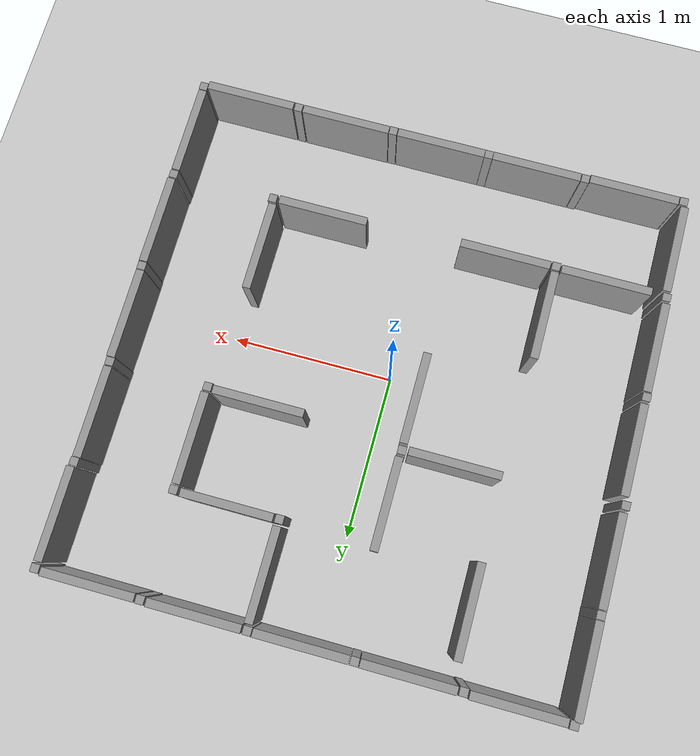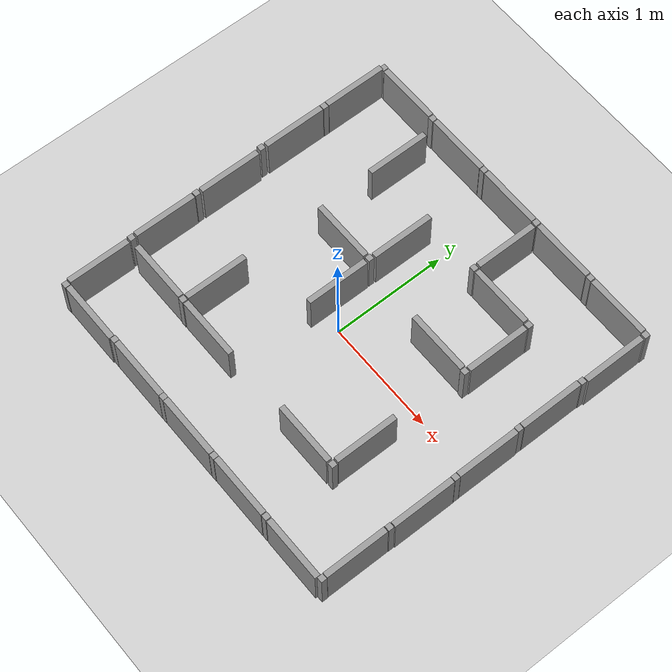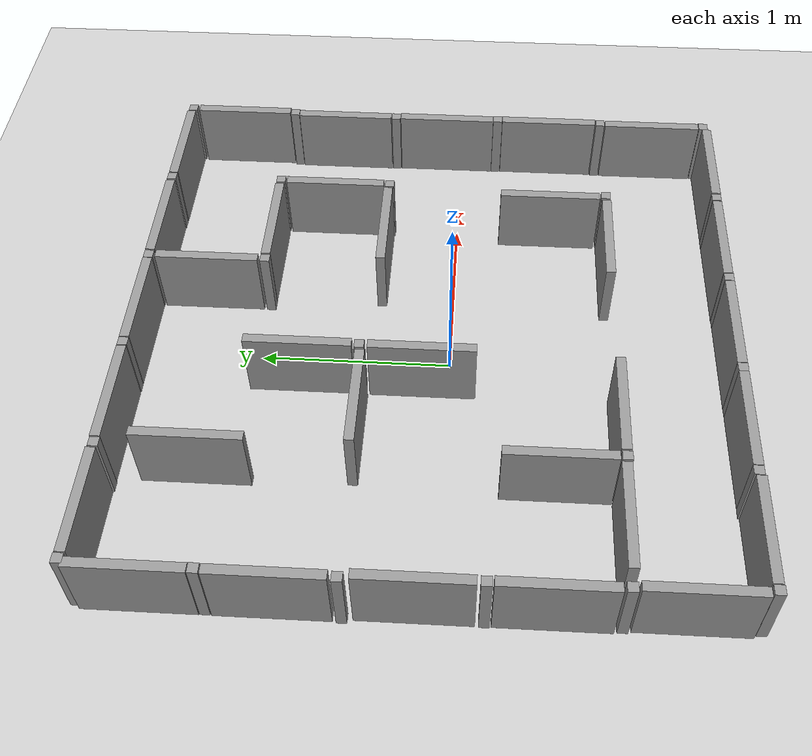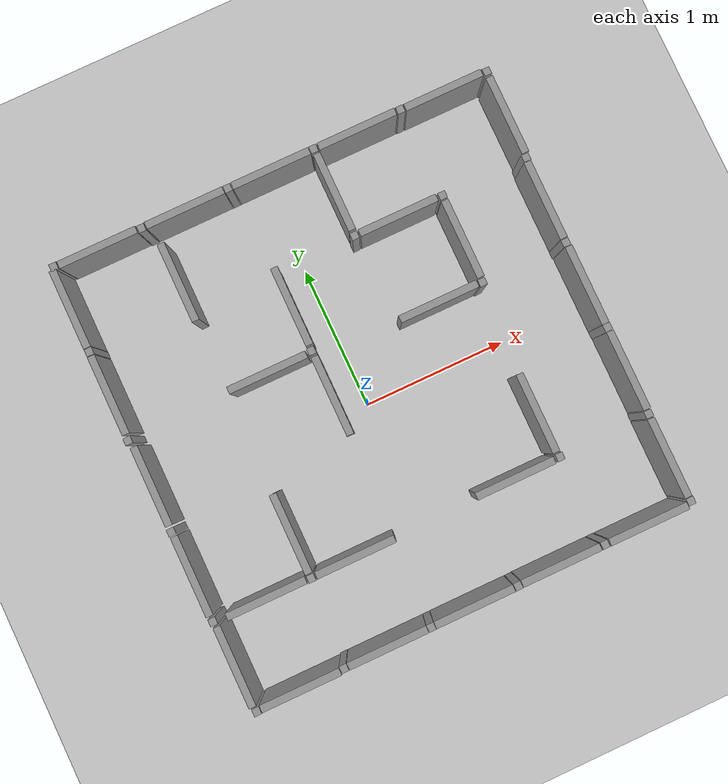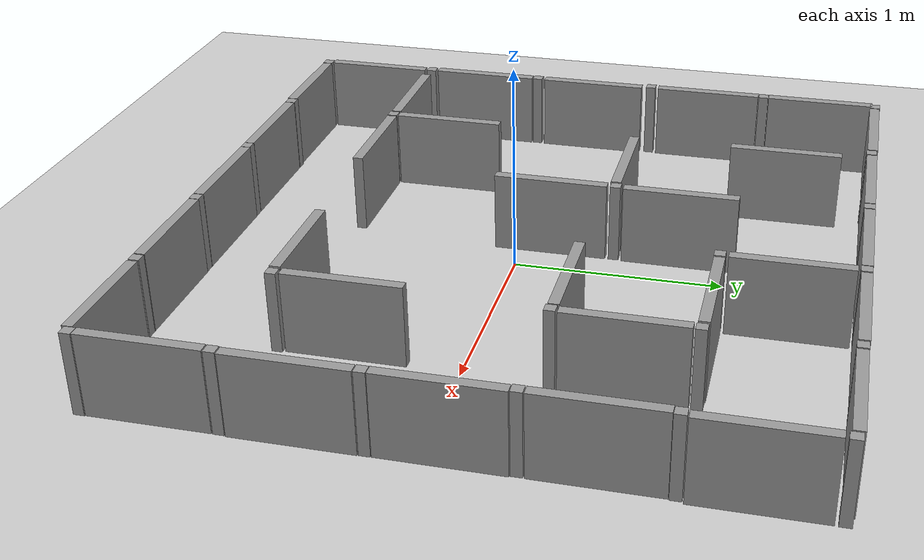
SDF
<sdf version="1.6">
 <world name="default">
  <light name="sun" type="directional">
   <pose>0 0 10 0 -0 0</pose>
   <diffuse>0.8 0.8 0.8 1</diffuse>
   <specular>0.2 0.2 0.2 1</specular>
   <attenuation>
    <range>1000</range>
    <constant>0.9</constant>
    <linear>0.01</linear>
    <quadratic>0.001</quadratic>
   </attenuation>
   <direction>-0.5 0.1 -0.9</direction>
  </light>
  <model name="ground_plane">
   <static>1</static>
   <link name="link">
    <collision name="collision">
     <geometry><plane><normal>0 0 1</normal><size>100 100</size></plane></geometry>
     <surface>
      <contact><collide_bitmask>65535</collide_bitmask></contact>
      <friction><ode><mu>100</mu><mu2>50</mu2></ode></friction>
     </surface>
    </collision>
    <visual name="visual">
     <cast_shadows>0</cast_shadows>
     <geometry><plane><normal>0 0 1</normal><size>100 100</size></plane></geometry>
     <material>
      <script><uri>file://media/materials/scripts/gazebo.material</uri><name>Gazebo/Grey</name></script>
     </material>
    </visual>
   </link>
  </model>
  <gravity>0 0 -9.8</gravity>
  <magnetic_field>6e-06 2.3e-05 -4.2e-05</magnetic_field>
  <atmosphere type="adiabatic"/>
  <physics name="default_physics" default="0" type="ode">
   <max_step_size>0.001</max_step_size>
   <real_time_factor>1</real_time_factor>
   <real_time_update_rate>1000</real_time_update_rate>
  </physics>
  <scene><ambient>0.4 0.4 0.4 1</ambient><background>0.7 0.7 0.7 1</background><shadows>1</shadows></scene>
  <audio><device>default</device></audio>
  <spherical_coordinates>
   <surface_model>EARTH_WGS84</surface_model>
   <latitude_deg>0</latitude_deg>
   <longitude_deg>0</longitude_deg>
   <elevation>0</elevation>
   <heading_deg>0</heading_deg>
  </spherical_coordinates>
  <model name="white_maze">
   <link name="link_0">
    <inertial>
     <mass>1</mass>
     <inertia>
      <ixx>0.166667</ixx>
      <ixy>0</ixy>
      <ixz>0</ixz>
      <iyy>0.166667</iyy>
      <iyz>0</iyz>
      <izz>0.166667</izz>
     </inertia>
    </inertial>
    <pose>-1.23382 -1.58127 0 0 -0 0</pose>
    <visual name="visual">
     <geometry><box><size>0.55 0.05 0.4</size></box></geometry>
     <material>
      <lighting>1</lighting>
      <script><uri>file://media/materials/scripts/gazebo.material</uri><name>Gazebo/Grey</name></script>
      <shader type="vertex"><normal_map>__default__</normal_map></shader>
      <ambient>1 1 1 1</ambient>
      <diffuse>0.7 0.7 0.7 1</diffuse>
      <specular>0.01 0.01 0.01 1</specular>
      <emissive>0 0 0 1</emissive>
     </material>
    </visual>
    <collision name="collision">
     <geometry><box><size>0.55 0.05 0.4</size></box></geometry>
     <surface>
      <friction>
       <ode><mu>1</mu><mu2>1</mu2><fdir1>0 0 0</fdir1><slip1>0</slip1><slip2>0</slip2></ode>
       <torsional>
        <coefficient>1</coefficient>
        <patch_radius>0</patch_radius>
        <surface_radius>0</surface_radius>
        <use_patch_radius>1</use_patch_radius>
        <ode><slip>0</slip></ode>
       </torsional>
      </friction>
      <bounce><restitution_coefficient>0</restitution_coefficient><threshold>1e+06</threshold></bounce>
      <contact>
       <collide_without_contact>0</collide_without_contact>
       <collide_without_contact_bitmask>1</collide_without_contact_bitmask>
       <collide_bitmask>1</collide_bitmask>
       <ode>
        <soft_cfm>0</soft_cfm>
        <soft_erp>0.2</soft_erp>
        <kp>1e+13</kp>
        <kd>1</kd>
        <max_vel>0.01</max_vel>
        <min_depth>0</min_depth>
       </ode>
       <bullet>
        <split_impulse>1</split_impulse>
        <split_impulse_penetration_threshold>-0.01</split_impulse_penetration_threshold>
        <soft_cfm>0</soft_cfm>
        <soft_erp>0.2</soft_erp>
        <kp>1e+13</kp>
        <kd>1</kd>
       </bullet>
      </contact>
     </surface>
    </collision>
   </link>
   <link name="link_0_clone">
    <inertial>
     <mass>1</mass>
     <inertia>
      <ixx>0.166667</ixx>
      <ixy>0</ixy>
      <ixz>0</ixz>
      <iyy>0.166667</iyy>
      <iyz>0</iyz>
      <izz>0.166667</izz>
     </inertia>
    </inertial>
    <pose>-0.627493 -1.57445 0 0 -0 0</pose>
    <visual name="visual">
     <geometry><box><size>0.55 0.05 0.4</size></box></geometry>
     <material>
      <lighting>1</lighting>
      <script><uri>file://media/materials/scripts/gazebo.material</uri><name>Gazebo/Grey</name></script>
      <shader type="vertex"><normal_map>__default__</normal_map></shader>
      <ambient>1 1 1 1</ambient>
      <diffuse>0.7 0.7 0.7 1</diffuse>
      <specular>0.01 0.01 0.01 1</specular>
      <emissive>0 0 0 1</emissive>
     </material>
    </visual>
    <collision name="collision">
     <geometry><box><size>0.55 0.05 0.4</size></box></geometry>
     <surface>
      <friction>
       <ode><mu>1</mu><mu2>1</mu2><fdir1>0 0 0</fdir1><slip1>0</slip1><slip2>0</slip2></ode>
       <torsional>
        <coefficient>1</coefficient>
        <patch_radius>0</patch_radius>
        <surface_radius>0</surface_radius>
        <use_patch_radius>1</use_patch_radius>
        <ode><slip>0</slip></ode>
       </torsional>
      </friction>
      <bounce><restitution_coefficient>0</restitution_coefficient><threshold>1e+06</threshold></bounce>
      <contact>
       <collide_without_contact>0</collide_without_contact>
       <collide_without_contact_bitmask>1</collide_without_contact_bitmask>
       <collide_bitmask>1</collide_bitmask>
       <ode>
        <soft_cfm>0</soft_cfm>
        <soft_erp>0.2</soft_erp>
        <kp>1e+13</kp>
        <kd>1</kd>
        <max_vel>0.01</max_vel>
        <min_depth>0</min_depth>
       </ode>
       <bullet>
        <split_impulse>1</split_impulse>
        <split_impulse_penetration_threshold>-0.01</split_impulse_penetration_threshold>
        <soft_cfm>0</soft_cfm>
        <soft_erp>0.2</soft_erp>
        <kp>1e+13</kp>
        <kd>1</kd>
       </bullet>
      </contact>
     </surface>
    </collision>
   </link>
   <link name="link_0_clone_0">
    <inertial>
     <mass>1</mass>
     <inertia>
      <ixx>0.166667</ixx>
      <ixy>0</ixy>
      <ixz>0</ixz>
      <iyy>0.166667</iyy>
      <iyz>0</iyz>
      <izz>0.166667</izz>
     </inertia>
    </inertial>
    <pose>-0.023747 -1.57344 0 0 -0 0</pose>
    <visual name="visual">
     <geometry><box><size>0.55 0.05 0.4</size></box></geometry>
     <material>
      <lighting>1</lighting>
      <script><uri>file://media/materials/scripts/gazebo.material</uri><name>Gazebo/Grey</name></script>
      <shader type="vertex"><normal_map>__default__</normal_map></shader>
      <ambient>1 1 1 1</ambient>
      <diffuse>0.7 0.7 0.7 1</diffuse>
      <specular>0.01 0.01 0.01 1</specular>
      <emissive>0 0 0 1</emissive>
     </material>
    </visual>
    <collision name="collision">
     <geometry><box><size>0.55 0.05 0.4</size></box></geometry>
     <surface>
      <friction>
       <ode><mu>1</mu><mu2>1</mu2><fdir1>0 0 0</fdir1><slip1>0</slip1><slip2>0</slip2></ode>
       <torsional>
        <coefficient>1</coefficient>
        <patch_radius>0</patch_radius>
        <surface_radius>0</surface_radius>
        <use_patch_radius>1</use_patch_radius>
        <ode><slip>0</slip></ode>
       </torsional>
      </friction>
      <bounce><restitution_coefficient>0</restitution_coefficient><threshold>1e+06</threshold></bounce>
      <contact>
       <collide_without_contact>0</collide_without_contact>
       <collide_without_contact_bitmask>1</collide_without_contact_bitmask>
       <collide_bitmask>1</collide_bitmask>
       <ode>
        <soft_cfm>0</soft_cfm>
        <soft_erp>0.2</soft_erp>
        <kp>1e+13</kp>
        <kd>1</kd>
        <max_vel>0.01</max_vel>
        <min_depth>0</min_depth>
       </ode>
       <bullet>
        <split_impulse>1</split_impulse>
        <split_impulse_penetration_threshold>-0.01</split_impulse_penetration_threshold>
        <soft_cfm>0</soft_cfm>
        <soft_erp>0.2</soft_erp>
        <kp>1e+13</kp>
        <kd>1</kd>
       </bullet>
      </contact>
     </surface>
    </collision>
   </link>
   <link name="link_0_clone_1">
    <inertial>
     <mass>1</mass>
     <inertia>
      <ixx>0.166667</ixx>
      <ixy>0</ixy>
      <ixz>0</ixz>
      <iyy>0.166667</iyy>
      <iyz>0</iyz>
      <izz>0.166667</izz>
     </inertia>
    </inertial>
    <pose>0.582587 -1.57153 0 0 -0 0</pose>
    <visual name="visual">
     <geometry><box><size>0.55 0.05 0.4</size></box></geometry>
     <material>
      <lighting>1</lighting>
      <script><uri>file://media/materials/scripts/gazebo.material</uri><name>Gazebo/Grey</name></script>
      <shader type="vertex"><normal_map>__default__</normal_map></shader>
      <ambient>1 1 1 1</ambient>
      <diffuse>0.7 0.7 0.7 1</diffuse>
      <specular>0.01 0.01 0.01 1</specular>
      <emissive>0 0 0 1</emissive>
     </material>
    </visual>
    <collision name="collision">
     <geometry><box><size>0.55 0.05 0.4</size></box></geometry>
     <surface>
      <friction>
       <ode><mu>1</mu><mu2>1</mu2><fdir1>0 0 0</fdir1><slip1>0</slip1><slip2>0</slip2></ode>
       <torsional>
        <coefficient>1</coefficient>
        <patch_radius>0</patch_radius>
        <surface_radius>0</surface_radius>
        <use_patch_radius>1</use_patch_radius>
        <ode><slip>0</slip></ode>
       </torsional>
      </friction>
      <bounce><restitution_coefficient>0</restitution_coefficient><threshold>1e+06</threshold></bounce>
      <contact>
       <collide_without_contact>0</collide_without_contact>
       <collide_without_contact_bitmask>1</collide_without_contact_bitmask>
       <collide_bitmask>1</collide_bitmask>
       <ode>
        <soft_cfm>0</soft_cfm>
        <soft_erp>0.2</soft_erp>
        <kp>1e+13</kp>
        <kd>1</kd>
        <max_vel>0.01</max_vel>
        <min_depth>0</min_depth>
       </ode>
       <bullet>
        <split_impulse>1</split_impulse>
        <split_impulse_penetration_threshold>-0.01</split_impulse_penetration_threshold>
        <soft_cfm>0</soft_cfm>
        <soft_erp>0.2</soft_erp>
        <kp>1e+13</kp>
        <kd>1</kd>
       </bullet>
      </contact>
     </surface>
    </collision>
   </link>
   <link name="link_0_clone_1_clone">
    <inertial>
     <mass>1</mass>
     <inertia>
      <ixx>0.166667</ixx>
      <ixy>0</ixy>
      <ixz>0</ixz>
      <iyy>0.166667</iyy>
      <iyz>0</iyz>
      <izz>0.166667</izz>
     </inertia>
    </inertial>
    <pose>1.49724 -1.25172 0 0 0 -1.57264</pose>
    <visual name="visual">
     <geometry><box><size>0.55 0.05 0.4</size></box></geometry>
     <material>
      <lighting>1</lighting>
      <script><uri>file://media/materials/scripts/gazebo.material</uri><name>Gazebo/Grey</name></script>
      <shader type="vertex"><normal_map>__default__</normal_map></shader>
      <ambient>1 1 1 1</ambient>
      <diffuse>0.7 0.7 0.7 1</diffuse>
      <specular>0.01 0.01 0.01 1</specular>
      <emissive>0 0 0 1</emissive>
     </material>
    </visual>
    <collision name="collision">
     <geometry><box><size>0.55 0.05 0.4</size></box></geometry>
     <surface>
      <friction>
       <ode><mu>1</mu><mu2>1</mu2><fdir1>0 0 0</fdir1><slip1>0</slip1><slip2>0</slip2></ode>
       <torsional>
        <coefficient>1</coefficient>
        <patch_radius>0</patch_radius>
        <surface_radius>0</surface_radius>
        <use_patch_radius>1</use_patch_radius>
        <ode><slip>0</slip></ode>
       </torsional>
      </friction>
      <bounce><restitution_coefficient>0</restitution_coefficient><threshold>1e+06</threshold></bounce>
      <contact>
       <collide_without_contact>0</collide_without_contact>
       <collide_without_contact_bitmask>1</collide_without_contact_bitmask>
       <collide_bitmask>1</collide_bitmask>
       <ode>
        <soft_cfm>0</soft_cfm>
        <soft_erp>0.2</soft_erp>
        <kp>1e+13</kp>
        <kd>1</kd>
        <max_vel>0.01</max_vel>
        <min_depth>0</min_depth>
       </ode>
       <bullet>
        <split_impulse>1</split_impulse>
        <split_impulse_penetration_threshold>-0.01</split_impulse_penetration_threshold>
        <soft_cfm>0</soft_cfm>
        <soft_erp>0.2</soft_erp>
        <kp>1e+13</kp>
        <kd>1</kd>
       </bullet>
      </contact>
     </surface>
    </collision>
   </link>
   <link name="link_0_clone_1_clone_0">
    <inertial>
     <mass>1</mass>
     <inertia>
      <ixx>0.166667</ixx>
      <ixy>0</ixy>
      <ixz>0</ixz>
      <iyy>0.166667</iyy>
      <iyz>0</iyz>
      <izz>0.166667</izz>
     </inertia>
    </inertial>
    <pose>1.21099 1.50565 0 0 -0 0</pose>
    <visual name="visual">
     <geometry><box><size>0.55 0.05 0.4</size></box></geometry>
     <material>
      <lighting>1</lighting>
      <script><uri>file://media/materials/scripts/gazebo.material</uri><name>Gazebo/Grey</name></script>
      <shader type="vertex"><normal_map>__default__</normal_map></shader>
      <ambient>1 1 1 1</ambient>
      <diffuse>0.7 0.7 0.7 1</diffuse>
      <specular>0.01 0.01 0.01 1</specular>
      <emissive>0 0 0 1</emissive>
     </material>
    </visual>
    <collision name="collision">
     <geometry><box><size>0.55 0.05 0.4</size></box></geometry>
     <surface>
      <friction>
       <ode><mu>1</mu><mu2>1</mu2><fdir1>0 0 0</fdir1><slip1>0</slip1><slip2>0</slip2></ode>
       <torsional>
        <coefficient>1</coefficient>
        <patch_radius>0</patch_radius>
        <surface_radius>0</surface_radius>
        <use_patch_radius>1</use_patch_radius>
        <ode><slip>0</slip></ode>
       </torsional>
      </friction>
      <bounce><restitution_coefficient>0</restitution_coefficient><threshold>1e+06</threshold></bounce>
      <contact>
       <collide_without_contact>0</collide_without_contact>
       <collide_without_contact_bitmask>1</collide_without_contact_bitmask>
       <collide_bitmask>1</collide_bitmask>
       <ode>
        <soft_cfm>0</soft_cfm>
        <soft_erp>0.2</soft_erp>
        <kp>1e+13</kp>
        <kd>1</kd>
        <max_vel>0.01</max_vel>
        <min_depth>0</min_depth>
       </ode>
       <bullet>
        <split_impulse>1</split_impulse>
        <split_impulse_penetration_threshold>-0.01</split_impulse_penetration_threshold>
        <soft_cfm>0</soft_cfm>
        <soft_erp>0.2</soft_erp>
        <kp>1e+13</kp>
        <kd>1</kd>
       </bullet>
      </contact>
     </surface>
    </collision>
   </link>
   <link name="link_0_clone_1_clone_1">
    <inertial>
     <mass>1</mass>
     <inertia>
      <ixx>0.166667</ixx>
      <ixy>0</ixy>
      <ixz>0</ixz>
      <iyy>0.166667</iyy>
      <iyz>0</iyz>
      <izz>0.166667</izz>
     </inertia>
    </inertial>
    <pose>0.593667 1.50999 0 0 -0 0</pose>
    <visual name="visual">
     <geometry><box><size>0.55 0.05 0.4</size></box></geometry>
     <material>
      <lighting>1</lighting>
      <script><uri>file://media/materials/scripts/gazebo.material</uri><name>Gazebo/Grey</name></script>
      <shader type="vertex"><normal_map>__default__</normal_map></shader>
      <ambient>1 1 1 1</ambient>
      <diffuse>0.7 0.7 0.7 1</diffuse>
      <specular>0.01 0.01 0.01 1</specular>
      <emissive>0 0 0 1</emissive>
     </material>
    </visual>
    <collision name="collision">
     <geometry><box><size>0.55 0.05 0.4</size></box></geometry>
     <surface>
      <friction>
       <ode><mu>1</mu><mu2>1</mu2><fdir1>0 0 0</fdir1><slip1>0</slip1><slip2>0</slip2></ode>
       <torsional>
        <coefficient>1</coefficient>
        <patch_radius>0</patch_radius>
        <surface_radius>0</surface_radius>
        <use_patch_radius>1</use_patch_radius>
        <ode><slip>0</slip></ode>
       </torsional>
      </friction>
      <bounce><restitution_coefficient>0</restitution_coefficient><threshold>1e+06</threshold></bounce>
      <contact>
       <collide_without_contact>0</collide_without_contact>
       <collide_without_contact_bitmask>1</collide_without_contact_bitmask>
       <collide_bitmask>1</collide_bitmask>
       <ode>
        <soft_cfm>0</soft_cfm>
        <soft_erp>0.2</soft_erp>
        <kp>1e+13</kp>
        <kd>1</kd>
        <max_vel>0.01</max_vel>
        <min_depth>0</min_depth>
       </ode>
       <bullet>
        <split_impulse>1</split_impulse>
        <split_impulse_penetration_threshold>-0.01</split_impulse_penetration_threshold>
        <soft_cfm>0</soft_cfm>
        <soft_erp>0.2</soft_erp>
        <kp>1e+13</kp>
        <kd>1</kd>
       </bullet>
      </contact>
     </surface>
    </collision>
   </link>
   <link name="link_0_clone_1_clone_2">
    <inertial>
     <mass>1</mass>
     <inertia>
      <ixx>0.166667</ixx>
      <ixy>0</ixy>
      <ixz>0</ixz>
      <iyy>0.166667</iyy>
      <iyz>0</iyz>
      <izz>0.166667</izz>
     </inertia>
    </inertial>
    <pose>-0.019419 1.51088 0 0 -0 0</pose>
    <visual name="visual">
     <geometry><box><size>0.55 0.05 0.4</size></box></geometry>
     <material>
      <lighting>1</lighting>
      <script><uri>file://media/materials/scripts/gazebo.material</uri><name>Gazebo/Grey</name></script>
      <shader type="vertex"><normal_map>__default__</normal_map></shader>
      <ambient>1 1 1 1</ambient>
      <diffuse>0.7 0.7 0.7 1</diffuse>
      <specular>0.01 0.01 0.01 1</specular>
      <emissive>0 0 0 1</emissive>
     </material>
    </visual>
    <collision name="collision">
     <geometry><box><size>0.55 0.05 0.4</size></box></geometry>
     <surface>
      <friction>
       <ode><mu>1</mu><mu2>1</mu2><fdir1>0 0 0</fdir1><slip1>0</slip1><slip2>0</slip2></ode>
       <torsional>
        <coefficient>1</coefficient>
        <patch_radius>0</patch_radius>
        <surface_radius>0</surface_radius>
        <use_patch_radius>1</use_patch_radius>
        <ode><slip>0</slip></ode>
       </torsional>
      </friction>
      <bounce><restitution_coefficient>0</restitution_coefficient><threshold>1e+06</threshold></bounce>
      <contact>
       <collide_without_contact>0</collide_without_contact>
       <collide_without_contact_bitmask>1</collide_without_contact_bitmask>
       <collide_bitmask>1</collide_bitmask>
       <ode>
        <soft_cfm>0</soft_cfm>
        <soft_erp>0.2</soft_erp>
        <kp>1e+13</kp>
        <kd>1</kd>
        <max_vel>0.01</max_vel>
        <min_depth>0</min_depth>
       </ode>
       <bullet>
        <split_impulse>1</split_impulse>
        <split_impulse_penetration_threshold>-0.01</split_impulse_penetration_threshold>
        <soft_cfm>0</soft_cfm>
        <soft_erp>0.2</soft_erp>
        <kp>1e+13</kp>
        <kd>1</kd>
       </bullet>
      </contact>
     </surface>
    </collision>
   </link>
   <link name="link_0_clone_1_clone_3">
    <inertial>
     <mass>1</mass>
     <inertia>
      <ixx>0.166667</ixx>
      <ixy>0</ixy>
      <ixz>0</ixz>
      <iyy>0.166667</iyy>
      <iyz>0</iyz>
      <izz>0.166667</izz>
     </inertia>
    </inertial>
    <pose>-0.630178 1.51122 0 0 -0 0</pose>
    <visual name="visual">
     <geometry><box><size>0.55 0.05 0.4</size></box></geometry>
     <material>
      <lighting>1</lighting>
      <script><uri>file://media/materials/scripts/gazebo.material</uri><name>Gazebo/Grey</name></script>
      <shader type="vertex"><normal_map>__default__</normal_map></shader>
      <ambient>1 1 1 1</ambient>
      <diffuse>0.7 0.7 0.7 1</diffuse>
      <specular>0.01 0.01 0.01 1</specular>
      <emissive>0 0 0 1</emissive>
     </material>
    </visual>
    <collision name="collision">
     <geometry><box><size>0.55 0.05 0.4</size></box></geometry>
     <surface>
      <friction>
       <ode><mu>1</mu><mu2>1</mu2><fdir1>0 0 0</fdir1><slip1>0</slip1><slip2>0</slip2></ode>
       <torsional>
        <coefficient>1</coefficient>
        <patch_radius>0</patch_radius>
        <surface_radius>0</surface_radius>
        <use_patch_radius>1</use_patch_radius>
        <ode><slip>0</slip></ode>
       </torsional>
      </friction>
      <bounce><restitution_coefficient>0</restitution_coefficient><threshold>1e+06</threshold></bounce>
      <contact>
       <collide_without_contact>0</collide_without_contact>
       <collide_without_contact_bitmask>1</collide_without_contact_bitmask>
       <collide_bitmask>1</collide_bitmask>
       <ode>
        <soft_cfm>0</soft_cfm>
        <soft_erp>0.2</soft_erp>
        <kp>1e+13</kp>
        <kd>1</kd>
        <max_vel>0.01</max_vel>
        <min_depth>0</min_depth>
       </ode>
       <bullet>
        <split_impulse>1</split_impulse>
        <split_impulse_penetration_threshold>-0.01</split_impulse_penetration_threshold>
        <soft_cfm>0</soft_cfm>
        <soft_erp>0.2</soft_erp>
        <kp>1e+13</kp>
        <kd>1</kd>
       </bullet>
      </contact>
     </surface>
    </collision>
   </link>
   <link name="link_0_clone_1_clone_4">
    <inertial>
     <mass>1</mass>
     <inertia>
      <ixx>0.166667</ixx>
      <ixy>0</ixy>
      <ixz>0</ixz>
      <iyy>0.166667</iyy>
      <iyz>0</iyz>
      <izz>0.166667</izz>
     </inertia>
    </inertial>
    <pose>-1.24431 1.51418 0 0 -0 0</pose>
    <visual name="visual">
     <geometry><box><size>0.55 0.05 0.4</size></box></geometry>
     <material>
      <lighting>1</lighting>
      <script><uri>file://media/materials/scripts/gazebo.material</uri><name>Gazebo/Grey</name></script>
      <shader type="vertex"><normal_map>__default__</normal_map></shader>
      <ambient>1 1 1 1</ambient>
      <diffuse>0.7 0.7 0.7 1</diffuse>
      <specular>0.01 0.01 0.01 1</specular>
      <emissive>0 0 0 1</emissive>
     </material>
    </visual>
    <collision name="collision">
     <geometry><box><size>0.55 0.05 0.4</size></box></geometry>
     <surface>
      <friction>
       <ode><mu>1</mu><mu2>1</mu2><fdir1>0 0 0</fdir1><slip1>0</slip1><slip2>0</slip2></ode>
       <torsional>
        <coefficient>1</coefficient>
        <patch_radius>0</patch_radius>
        <surface_radius>0</surface_radius>
        <use_patch_radius>1</use_patch_radius>
        <ode><slip>0</slip></ode>
       </torsional>
      </friction>
      <bounce><restitution_coefficient>0</restitution_coefficient><threshold>1e+06</threshold></bounce>
      <contact>
       <collide_without_contact>0</collide_without_contact>
       <collide_without_contact_bitmask>1</collide_without_contact_bitmask>
       <collide_bitmask>1</collide_bitmask>
       <ode>
        <soft_cfm>0</soft_cfm>
        <soft_erp>0.2</soft_erp>
        <kp>1e+13</kp>
        <kd>1</kd>
        <max_vel>0.01</max_vel>
        <min_depth>0</min_depth>
       </ode>
       <bullet>
        <split_impulse>1</split_impulse>
        <split_impulse_penetration_threshold>-0.01</split_impulse_penetration_threshold>
        <soft_cfm>0</soft_cfm>
        <soft_erp>0.2</soft_erp>
        <kp>1e+13</kp>
        <kd>1</kd>
       </bullet>
      </contact>
     </surface>
    </collision>
   </link>
   <link name="link_0_clone_1_clone_clone">
    <inertial>
     <mass>1</mass>
     <inertia>
      <ixx>0.166667</ixx>
      <ixy>0</ixy>
      <ixz>0</ixz>
      <iyy>0.166667</iyy>
      <iyz>0</iyz>
      <izz>0.166667</izz>
     </inertia>
    </inertial>
    <pose>1.504 -0.640018 0 0 0 -1.57264</pose>
    <visual name="visual">
     <geometry><box><size>0.55 0.05 0.4</size></box></geometry>
     <material>
      <lighting>1</lighting>
      <script><uri>file://media/materials/scripts/gazebo.material</uri><name>Gazebo/Grey</name></script>
      <shader type="vertex"><normal_map>__default__</normal_map></shader>
      <ambient>1 1 1 1</ambient>
      <diffuse>0.7 0.7 0.7 1</diffuse>
      <specular>0.01 0.01 0.01 1</specular>
      <emissive>0 0 0 1</emissive>
     </material>
    </visual>
    <collision name="collision">
     <geometry><box><size>0.55 0.05 0.4</size></box></geometry>
     <surface>
      <friction>
       <ode><mu>1</mu><mu2>1</mu2><fdir1>0 0 0</fdir1><slip1>0</slip1><slip2>0</slip2></ode>
       <torsional>
        <coefficient>1</coefficient>
        <patch_radius>0</patch_radius>
        <surface_radius>0</surface_radius>
        <use_patch_radius>1</use_patch_radius>
        <ode><slip>0</slip></ode>
       </torsional>
      </friction>
      <bounce><restitution_coefficient>0</restitution_coefficient><threshold>1e+06</threshold></bounce>
      <contact>
       <collide_without_contact>0</collide_without_contact>
       <collide_without_contact_bitmask>1</collide_without_contact_bitmask>
       <collide_bitmask>1</collide_bitmask>
       <ode>
        <soft_cfm>0</soft_cfm>
        <soft_erp>0.2</soft_erp>
        <kp>1e+13</kp>
        <kd>1</kd>
        <max_vel>0.01</max_vel>
        <min_depth>0</min_depth>
       </ode>
       <bullet>
        <split_impulse>1</split_impulse>
        <split_impulse_penetration_threshold>-0.01</split_impulse_penetration_threshold>
        <soft_cfm>0</soft_cfm>
        <soft_erp>0.2</soft_erp>
        <kp>1e+13</kp>
        <kd>1</kd>
       </bullet>
      </contact>
     </surface>
    </collision>
   </link>
   <link name="link_0_clone_1_clone_clone_0">
    <inertial>
     <mass>1</mass>
     <inertia>
      <ixx>0.166667</ixx>
      <ixy>0</ixy>
      <ixz>0</ixz>
      <iyy>0.166667</iyy>
      <iyz>0</iyz>
      <izz>0.166667</izz>
     </inertia>
    </inertial>
    <pose>1.50232 -0.033133 0 0 0 -1.57264</pose>
    <visual name="visual">
     <geometry><box><size>0.55 0.05 0.4</size></box></geometry>
     <material>
      <lighting>1</lighting>
      <script><uri>file://media/materials/scripts/gazebo.material</uri><name>Gazebo/Grey</name></script>
      <shader type="vertex"><normal_map>__default__</normal_map></shader>
      <ambient>1 1 1 1</ambient>
      <diffuse>0.7 0.7 0.7 1</diffuse>
      <specular>0.01 0.01 0.01 1</specular>
      <emissive>0 0 0 1</emissive>
     </material>
    </visual>
    <collision name="collision">
     <geometry><box><size>0.55 0.05 0.4</size></box></geometry>
     <surface>
      <friction>
       <ode><mu>1</mu><mu2>1</mu2><fdir1>0 0 0</fdir1><slip1>0</slip1><slip2>0</slip2></ode>
       <torsional>
        <coefficient>1</coefficient>
        <patch_radius>0</patch_radius>
        <surface_radius>0</surface_radius>
        <use_patch_radius>1</use_patch_radius>
        <ode><slip>0</slip></ode>
       </torsional>
      </friction>
      <bounce><restitution_coefficient>0</restitution_coefficient><threshold>1e+06</threshold></bounce>
      <contact>
       <collide_without_contact>0</collide_without_contact>
       <collide_without_contact_bitmask>1</collide_without_contact_bitmask>
       <collide_bitmask>1</collide_bitmask>
       <ode>
        <soft_cfm>0</soft_cfm>
        <soft_erp>0.2</soft_erp>
        <kp>1e+13</kp>
        <kd>1</kd>
        <max_vel>0.01</max_vel>
        <min_depth>0</min_depth>
       </ode>
       <bullet>
        <split_impulse>1</split_impulse>
        <split_impulse_penetration_threshold>-0.01</split_impulse_penetration_threshold>
        <soft_cfm>0</soft_cfm>
        <soft_erp>0.2</soft_erp>
        <kp>1e+13</kp>
        <kd>1</kd>
       </bullet>
      </contact>
     </surface>
    </collision>
   </link>
   <link name="link_0_clone_1_clone_clone_1">
    <inertial>
     <mass>1</mass>
     <inertia>
      <ixx>0.166667</ixx>
      <ixy>0</ixy>
      <ixz>0</ixz>
      <iyy>0.166667</iyy>
      <iyz>0</iyz>
      <izz>0.166667</izz>
     </inertia>
    </inertial>
    <pose>1.49955 0.57556 0 0 0 -1.57264</pose>
    <visual name="visual">
     <geometry><box><size>0.55 0.05 0.4</size></box></geometry>
     <material>
      <lighting>1</lighting>
      <script><uri>file://media/materials/scripts/gazebo.material</uri><name>Gazebo/Grey</name></script>
      <shader type="vertex"><normal_map>__default__</normal_map></shader>
      <ambient>1 1 1 1</ambient>
      <diffuse>0.7 0.7 0.7 1</diffuse>
      <specular>0.01 0.01 0.01 1</specular>
      <emissive>0 0 0 1</emissive>
     </material>
    </visual>
    <collision name="collision">
     <geometry><box><size>0.55 0.05 0.4</size></box></geometry>
     <surface>
      <friction>
       <ode><mu>1</mu><mu2>1</mu2><fdir1>0 0 0</fdir1><slip1>0</slip1><slip2>0</slip2></ode>
       <torsional>
        <coefficient>1</coefficient>
        <patch_radius>0</patch_radius>
        <surface_radius>0</surface_radius>
        <use_patch_radius>1</use_patch_radius>
        <ode><slip>0</slip></ode>
       </torsional>
      </friction>
      <bounce><restitution_coefficient>0</restitution_coefficient><threshold>1e+06</threshold></bounce>
      <contact>
       <collide_without_contact>0</collide_without_contact>
       <collide_without_contact_bitmask>1</collide_without_contact_bitmask>
       <collide_bitmask>1</collide_bitmask>
       <ode>
        <soft_cfm>0</soft_cfm>
        <soft_erp>0.2</soft_erp>
        <kp>1e+13</kp>
        <kd>1</kd>
        <max_vel>0.01</max_vel>
        <min_depth>0</min_depth>
       </ode>
       <bullet>
        <split_impulse>1</split_impulse>
        <split_impulse_penetration_threshold>-0.01</split_impulse_penetration_threshold>
        <soft_cfm>0</soft_cfm>
        <soft_erp>0.2</soft_erp>
        <kp>1e+13</kp>
        <kd>1</kd>
       </bullet>
      </contact>
     </surface>
    </collision>
   </link>
   <link name="link_0_clone_1_clone_clone_1_clone">
    <inertial>
     <mass>1</mass>
     <inertia>
      <ixx>0.166667</ixx>
      <ixy>0</ixy>
      <ixz>0</ixz>
      <iyy>0.166667</iyy>
      <iyz>0</iyz>
      <izz>0.166667</izz>
     </inertia>
    </inertial>
    <pose>-1.54904 -1.27572 0 0 0 -1.57264</pose>
    <visual name="visual">
     <geometry><box><size>0.55 0.05 0.4</size></box></geometry>
     <material>
      <lighting>1</lighting>
      <script><uri>file://media/materials/scripts/gazebo.material</uri><name>Gazebo/Grey</name></script>
      <shader type="vertex"><normal_map>__default__</normal_map></shader>
      <ambient>1 1 1 1</ambient>
      <diffuse>0.7 0.7 0.7 1</diffuse>
      <specular>0.01 0.01 0.01 1</specular>
      <emissive>0 0 0 1</emissive>
     </material>
    </visual>
    <collision name="collision">
     <geometry><box><size>0.55 0.05 0.4</size></box></geometry>
     <surface>
      <friction>
       <ode><mu>1</mu><mu2>1</mu2><fdir1>0 0 0</fdir1><slip1>0</slip1><slip2>0</slip2></ode>
       <torsional>
        <coefficient>1</coefficient>
        <patch_radius>0</patch_radius>
        <surface_radius>0</surface_radius>
        <use_patch_radius>1</use_patch_radius>
        <ode><slip>0</slip></ode>
       </torsional>
      </friction>
      <bounce><restitution_coefficient>0</restitution_coefficient><threshold>1e+06</threshold></bounce>
      <contact>
       <collide_without_contact>0</collide_without_contact>
       <collide_without_contact_bitmask>1</collide_without_contact_bitmask>
       <collide_bitmask>1</collide_bitmask>
       <ode>
        <soft_cfm>0</soft_cfm>
        <soft_erp>0.2</soft_erp>
        <kp>1e+13</kp>
        <kd>1</kd>
        <max_vel>0.01</max_vel>
        <min_depth>0</min_depth>
       </ode>
       <bullet>
        <split_impulse>1</split_impulse>
        <split_impulse_penetration_threshold>-0.01</split_impulse_penetration_threshold>
        <soft_cfm>0</soft_cfm>
        <soft_erp>0.2</soft_erp>
        <kp>1e+13</kp>
        <kd>1</kd>
       </bullet>
      </contact>
     </surface>
    </collision>
   </link>
   <link name="link_0_clone_1_clone_clone_1_clone_0">
    <inertial>
     <mass>1</mass>
     <inertia>
      <ixx>0.166667</ixx>
      <ixy>0</ixy>
      <ixz>0</ixz>
      <iyy>0.166667</iyy>
      <iyz>0</iyz>
      <izz>0.166667</izz>
     </inertia>
    </inertial>
    <pose>-1.55915 -0.649577 0 0 0 -1.57264</pose>
    <visual name="visual">
     <geometry><box><size>0.55 0.05 0.4</size></box></geometry>
     <material>
      <lighting>1</lighting>
      <script><uri>file://media/materials/scripts/gazebo.material</uri><name>Gazebo/Grey</name></script>
      <shader type="vertex"><normal_map>__default__</normal_map></shader>
      <ambient>1 1 1 1</ambient>
      <diffuse>0.7 0.7 0.7 1</diffuse>
      <specular>0.01 0.01 0.01 1</specular>
      <emissive>0 0 0 1</emissive>
     </material>
    </visual>
    <collision name="collision">
     <geometry><box><size>0.55 0.05 0.4</size></box></geometry>
     <surface>
      <friction>
       <ode><mu>1</mu><mu2>1</mu2><fdir1>0 0 0</fdir1><slip1>0</slip1><slip2>0</slip2></ode>
       <torsional>
        <coefficient>1</coefficient>
        <patch_radius>0</patch_radius>
        <surface_radius>0</surface_radius>
        <use_patch_radius>1</use_patch_radius>
        <ode><slip>0</slip></ode>
       </torsional>
      </friction>
      <bounce><restitution_coefficient>0</restitution_coefficient><threshold>1e+06</threshold></bounce>
      <contact>
       <collide_without_contact>0</collide_without_contact>
       <collide_without_contact_bitmask>1</collide_without_contact_bitmask>
       <collide_bitmask>1</collide_bitmask>
       <ode>
        <soft_cfm>0</soft_cfm>
        <soft_erp>0.2</soft_erp>
        <kp>1e+13</kp>
        <kd>1</kd>
        <max_vel>0.01</max_vel>
        <min_depth>0</min_depth>
       </ode>
       <bullet>
        <split_impulse>1</split_impulse>
        <split_impulse_penetration_threshold>-0.01</split_impulse_penetration_threshold>
        <soft_cfm>0</soft_cfm>
        <soft_erp>0.2</soft_erp>
        <kp>1e+13</kp>
        <kd>1</kd>
       </bullet>
      </contact>
     </surface>
    </collision>
   </link>
   <link name="link_0_clone_1_clone_clone_1_clone_0_clone">
    <inertial>
     <mass>1</mass>
     <inertia>
      <ixx>0.166667</ixx>
      <ixy>0</ixy>
      <ixz>0</ixz>
      <iyy>0.166667</iyy>
      <iyz>0</iyz>
      <izz>0.166667</izz>
     </inertia>
    </inertial>
    <pose>-0.883039 -0.671172 0 0 0 -1.57264</pose>
    <visual name="visual">
     <geometry><box><size>0.55 0.05 0.4</size></box></geometry>
     <material>
      <lighting>1</lighting>
      <script><uri>file://media/materials/scripts/gazebo.material</uri><name>Gazebo/Grey</name></script>
      <shader type="vertex"><normal_map>__default__</normal_map></shader>
      <ambient>1 1 1 1</ambient>
      <diffuse>0.7 0.7 0.7 1</diffuse>
      <specular>0.01 0.01 0.01 1</specular>
      <emissive>0 0 0 1</emissive>
     </material>
    </visual>
    <collision name="collision">
     <geometry><box><size>0.55 0.05 0.4</size></box></geometry>
     <surface>
      <friction>
       <ode><mu>1</mu><mu2>1</mu2><fdir1>0 0 0</fdir1><slip1>0</slip1><slip2>0</slip2></ode>
       <torsional>
        <coefficient>1</coefficient>
        <patch_radius>0</patch_radius>
        <surface_radius>0</surface_radius>
        <use_patch_radius>1</use_patch_radius>
        <ode><slip>0</slip></ode>
       </torsional>
      </friction>
      <bounce><restitution_coefficient>0</restitution_coefficient><threshold>1e+06</threshold></bounce>
      <contact>
       <collide_without_contact>0</collide_without_contact>
       <collide_without_contact_bitmask>1</collide_without_contact_bitmask>
       <collide_bitmask>1</collide_bitmask>
       <ode>
        <soft_cfm>0</soft_cfm>
        <soft_erp>0.2</soft_erp>
        <kp>1e+13</kp>
        <kd>1</kd>
        <max_vel>0.01</max_vel>
        <min_depth>0</min_depth>
       </ode>
       <bullet>
        <split_impulse>1</split_impulse>
        <split_impulse_penetration_threshold>-0.01</split_impulse_penetration_threshold>
        <soft_cfm>0</soft_cfm>
        <soft_erp>0.2</soft_erp>
        <kp>1e+13</kp>
        <kd>1</kd>
       </bullet>
      </contact>
     </surface>
    </collision>
   </link>
   <link name="link_0_clone_1_clone_clone_1_clone_0_clone_clone">
    <inertial>
     <mass>1</mass>
     <inertia>
      <ixx>0.166667</ixx>
      <ixy>0</ixy>
      <ixz>0</ixz>
      <iyy>0.166667</iyy>
      <iyz>0</iyz>
      <izz>0.166667</izz>
     </inertia>
    </inertial>
    <pose>-0.276196 0.011056 0 0 0 -1.57264</pose>
    <visual name="visual">
     <geometry><box><size>0.55 0.05 0.4</size></box></geometry>
     <material>
      <lighting>1</lighting>
      <script><uri>file://media/materials/scripts/gazebo.material</uri><name>Gazebo/Grey</name></script>
      <shader type="vertex"><normal_map>__default__</normal_map></shader>
      <ambient>1 1 1 1</ambient>
      <diffuse>0.7 0.7 0.7 1</diffuse>
      <specular>0.01 0.01 0.01 1</specular>
      <emissive>0 0 0 1</emissive>
     </material>
    </visual>
    <collision name="collision">
     <geometry><box><size>0.55 0.05 0.4</size></box></geometry>
     <surface>
      <friction>
       <ode><mu>1</mu><mu2>1</mu2><fdir1>0 0 0</fdir1><slip1>0</slip1><slip2>0</slip2></ode>
       <torsional>
        <coefficient>1</coefficient>
        <patch_radius>0</patch_radius>
        <surface_radius>0</surface_radius>
        <use_patch_radius>1</use_patch_radius>
        <ode><slip>0</slip></ode>
       </torsional>
      </friction>
      <bounce><restitution_coefficient>0</restitution_coefficient><threshold>1e+06</threshold></bounce>
      <contact>
       <collide_without_contact>0</collide_without_contact>
       <collide_without_contact_bitmask>1</collide_without_contact_bitmask>
       <collide_bitmask>1</collide_bitmask>
       <ode>
        <soft_cfm>0</soft_cfm>
        <soft_erp>0.2</soft_erp>
        <kp>1e+13</kp>
        <kd>1</kd>
        <max_vel>0.01</max_vel>
        <min_depth>0</min_depth>
       </ode>
       <bullet>
        <split_impulse>1</split_impulse>
        <split_impulse_penetration_threshold>-0.01</split_impulse_penetration_threshold>
        <soft_cfm>0</soft_cfm>
        <soft_erp>0.2</soft_erp>
        <kp>1e+13</kp>
        <kd>1</kd>
       </bullet>
      </contact>
     </surface>
    </collision>
   </link>
   <link name="link_0_clone_1_clone_clone_1_clone_0_clone_clone_0">
    <inertial>
     <mass>1</mass>
     <inertia>
      <ixx>0.166667</ixx>
      <ixy>0</ixy>
      <ixz>0</ixz>
      <iyy>0.166667</iyy>
      <iyz>0</iyz>
      <izz>0.166667</izz>
     </inertia>
    </inertial>
    <pose>-0.271946 0.640841 0 0 0 -1.57264</pose>
    <visual name="visual">
     <geometry><box><size>0.55 0.05 0.4</size></box></geometry>
     <material>
      <lighting>1</lighting>
      <script><uri>file://media/materials/scripts/gazebo.material</uri><name>Gazebo/Grey</name></script>
      <shader type="vertex"><normal_map>__default__</normal_map></shader>
      <ambient>1 1 1 1</ambient>
      <diffuse>0.7 0.7 0.7 1</diffuse>
      <specular>0.01 0.01 0.01 1</specular>
      <emissive>0 0 0 1</emissive>
     </material>
    </visual>
    <collision name="collision">
     <geometry><box><size>0.55 0.05 0.4</size></box></geometry>
     <surface>
      <friction>
       <ode><mu>1</mu><mu2>1</mu2><fdir1>0 0 0</fdir1><slip1>0</slip1><slip2>0</slip2></ode>
       <torsional>
        <coefficient>1</coefficient>
        <patch_radius>0</patch_radius>
        <surface_radius>0</surface_radius>
        <use_patch_radius>1</use_patch_radius>
        <ode><slip>0</slip></ode>
       </torsional>
      </friction>
      <bounce><restitution_coefficient>0</restitution_coefficient><threshold>1e+06</threshold></bounce>
      <contact>
       <collide_without_contact>0</collide_without_contact>
       <collide_without_contact_bitmask>1</collide_without_contact_bitmask>
       <collide_bitmask>1</collide_bitmask>
       <ode>
        <soft_cfm>0</soft_cfm>
        <soft_erp>0.2</soft_erp>
        <kp>1e+13</kp>
        <kd>1</kd>
        <max_vel>0.01</max_vel>
        <min_depth>0</min_depth>
       </ode>
       <bullet>
        <split_impulse>1</split_impulse>
        <split_impulse_penetration_threshold>-0.01</split_impulse_penetration_threshold>
        <soft_cfm>0</soft_cfm>
        <soft_erp>0.2</soft_erp>
        <kp>1e+13</kp>
        <kd>1</kd>
       </bullet>
      </contact>
     </surface>
    </collision>
   </link>
   <link name="link_0_clone_1_clone_clone_1_clone_0_clone_clone_1">
    <inertial>
     <mass>1</mass>
     <inertia>
      <ixx>0.166667</ixx>
      <ixy>0</ixy>
      <ixz>0</ixz>
      <iyy>0.166667</iyy>
      <iyz>0</iyz>
      <izz>0.166667</izz>
     </inertia>
    </inertial>
    <pose>0.908057 0.57311 0 0 0 -1.57264</pose>
    <visual name="visual">
     <geometry><box><size>0.55 0.05 0.4</size></box></geometry>
     <material>
      <lighting>1</lighting>
      <script><uri>file://media/materials/scripts/gazebo.material</uri><name>Gazebo/Grey</name></script>
      <shader type="vertex"><normal_map>__default__</normal_map></shader>
      <ambient>1 1 1 1</ambient>
      <diffuse>0.7 0.7 0.7 1</diffuse>
      <specular>0.01 0.01 0.01 1</specular>
      <emissive>0 0 0 1</emissive>
     </material>
    </visual>
    <collision name="collision">
     <geometry><box><size>0.55 0.05 0.4</size></box></geometry>
     <surface>
      <friction>
       <ode><mu>1</mu><mu2>1</mu2><fdir1>0 0 0</fdir1><slip1>0</slip1><slip2>0</slip2></ode>
       <torsional>
        <coefficient>1</coefficient>
        <patch_radius>0</patch_radius>
        <surface_radius>0</surface_radius>
        <use_patch_radius>1</use_patch_radius>
        <ode><slip>0</slip></ode>
       </torsional>
      </friction>
      <bounce><restitution_coefficient>0</restitution_coefficient><threshold>1e+06</threshold></bounce>
      <contact>
       <collide_without_contact>0</collide_without_contact>
       <collide_without_contact_bitmask>1</collide_without_contact_bitmask>
       <collide_bitmask>1</collide_bitmask>
       <ode>
        <soft_cfm>0</soft_cfm>
        <soft_erp>0.2</soft_erp>
        <kp>1e+13</kp>
        <kd>1</kd>
        <max_vel>0.01</max_vel>
        <min_depth>0</min_depth>
       </ode>
       <bullet>
        <split_impulse>1</split_impulse>
        <split_impulse_penetration_threshold>-0.01</split_impulse_penetration_threshold>
        <soft_cfm>0</soft_cfm>
        <soft_erp>0.2</soft_erp>
        <kp>1e+13</kp>
        <kd>1</kd>
       </bullet>
      </contact>
     </surface>
    </collision>
   </link>
   <link name="link_0_clone_1_clone_clone_1_clone_0_clone_clone_2">
    <inertial>
     <mass>1</mass>
     <inertia>
      <ixx>0.166667</ixx>
      <ixy>0</ixy>
      <ixz>0</ixz>
      <iyy>0.166667</iyy>
      <iyz>0</iyz>
      <izz>0.166667</izz>
     </inertia>
    </inertial>
    <pose>0.28851 1.19873 0 0 0 -1.57264</pose>
    <visual name="visual">
     <geometry><box><size>0.55 0.05 0.4</size></box></geometry>
     <material>
      <lighting>1</lighting>
      <script><uri>file://media/materials/scripts/gazebo.material</uri><name>Gazebo/Grey</name></script>
      <shader type="vertex"><normal_map>__default__</normal_map></shader>
      <ambient>1 1 1 1</ambient>
      <diffuse>0.7 0.7 0.7 1</diffuse>
      <specular>0.01 0.01 0.01 1</specular>
      <emissive>0 0 0 1</emissive>
     </material>
    </visual>
    <collision name="collision">
     <geometry><box><size>0.55 0.05 0.4</size></box></geometry>
     <surface>
      <friction>
       <ode><mu>1</mu><mu2>1</mu2><fdir1>0 0 0</fdir1><slip1>0</slip1><slip2>0</slip2></ode>
       <torsional>
        <coefficient>1</coefficient>
        <patch_radius>0</patch_radius>
        <surface_radius>0</surface_radius>
        <use_patch_radius>1</use_patch_radius>
        <ode><slip>0</slip></ode>
       </torsional>
      </friction>
      <bounce><restitution_coefficient>0</restitution_coefficient><threshold>1e+06</threshold></bounce>
      <contact>
       <collide_without_contact>0</collide_without_contact>
       <collide_without_contact_bitmask>1</collide_without_contact_bitmask>
       <collide_bitmask>1</collide_bitmask>
       <ode>
        <soft_cfm>0</soft_cfm>
        <soft_erp>0.2</soft_erp>
        <kp>1e+13</kp>
        <kd>1</kd>
        <max_vel>0.01</max_vel>
        <min_depth>0</min_depth>
       </ode>
       <bullet>
        <split_impulse>1</split_impulse>
        <split_impulse_penetration_threshold>-0.01</split_impulse_penetration_threshold>
        <soft_cfm>0</soft_cfm>
        <soft_erp>0.2</soft_erp>
        <kp>1e+13</kp>
        <kd>1</kd>
       </bullet>
      </contact>
     </surface>
    </collision>
   </link>
   <link name="link_0_clone_1_clone_clone_1_clone_0_clone_clone_3">
    <inertial>
     <mass>1</mass>
     <inertia>
      <ixx>0.166667</ixx>
      <ixy>0</ixy>
      <ixz>0</ixz>
      <iyy>0.166667</iyy>
      <iyz>0</iyz>
      <izz>0.166667</izz>
     </inertia>
    </inertial>
    <pose>-0.86681 1.09005 0 0 0 -1.57264</pose>
    <visual name="visual">
     <geometry><box><size>0.55 0.05 0.4</size></box></geometry>
     <material>
      <lighting>1</lighting>
      <script><uri>file://media/materials/scripts/gazebo.material</uri><name>Gazebo/Grey</name></script>
      <shader type="vertex"><normal_map>__default__</normal_map></shader>
      <ambient>1 1 1 1</ambient>
      <diffuse>0.7 0.7 0.7 1</diffuse>
      <specular>0.01 0.01 0.01 1</specular>
      <emissive>0 0 0 1</emissive>
     </material>
    </visual>
    <collision name="collision">
     <geometry><box><size>0.55 0.05 0.4</size></box></geometry>
     <surface>
      <friction>
       <ode><mu>1</mu><mu2>1</mu2><fdir1>0 0 0</fdir1><slip1>0</slip1><slip2>0</slip2></ode>
       <torsional>
        <coefficient>1</coefficient>
        <patch_radius>0</patch_radius>
        <surface_radius>0</surface_radius>
        <use_patch_radius>1</use_patch_radius>
        <ode><slip>0</slip></ode>
       </torsional>
      </friction>
      <bounce><restitution_coefficient>0</restitution_coefficient><threshold>1e+06</threshold></bounce>
      <contact>
       <collide_without_contact>0</collide_without_contact>
       <collide_without_contact_bitmask>1</collide_without_contact_bitmask>
       <collide_bitmask>1</collide_bitmask>
       <ode>
        <soft_cfm>0</soft_cfm>
        <soft_erp>0.2</soft_erp>
        <kp>1e+13</kp>
        <kd>1</kd>
        <max_vel>0.01</max_vel>
        <min_depth>0</min_depth>
       </ode>
       <bullet>
        <split_impulse>1</split_impulse>
        <split_impulse_penetration_threshold>-0.01</split_impulse_penetration_threshold>
        <soft_cfm>0</soft_cfm>
        <soft_erp>0.2</soft_erp>
        <kp>1e+13</kp>
        <kd>1</kd>
       </bullet>
      </contact>
     </surface>
    </collision>
   </link>
   <link name="link_0_clone_1_clone_clone_1_clone_1">
    <inertial>
     <mass>1</mass>
     <inertia>
      <ixx>0.166667</ixx>
      <ixy>0</ixy>
      <ixz>0</ixz>
      <iyy>0.166667</iyy>
      <iyz>0</iyz>
      <izz>0.166667</izz>
     </inertia>
    </inertial>
    <pose>-1.55831 -0.025932 0 0 0 -1.57264</pose>
    <visual name="visual">
     <geometry><box><size>0.55 0.05 0.4</size></box></geometry>
     <material>
      <lighting>1</lighting>
      <script><uri>file://media/materials/scripts/gazebo.material</uri><name>Gazebo/Grey</name></script>
      <shader type="vertex"><normal_map>__default__</normal_map></shader>
      <ambient>1 1 1 1</ambient>
      <diffuse>0.7 0.7 0.7 1</diffuse>
      <specular>0.01 0.01 0.01 1</specular>
      <emissive>0 0 0 1</emissive>
     </material>
    </visual>
    <collision name="collision">
     <geometry><box><size>0.55 0.05 0.4</size></box></geometry>
     <surface>
      <friction>
       <ode><mu>1</mu><mu2>1</mu2><fdir1>0 0 0</fdir1><slip1>0</slip1><slip2>0</slip2></ode>
       <torsional>
        <coefficient>1</coefficient>
        <patch_radius>0</patch_radius>
        <surface_radius>0</surface_radius>
        <use_patch_radius>1</use_patch_radius>
        <ode><slip>0</slip></ode>
       </torsional>
      </friction>
      <bounce><restitution_coefficient>0</restitution_coefficient><threshold>1e+06</threshold></bounce>
      <contact>
       <collide_without_contact>0</collide_without_contact>
       <collide_without_contact_bitmask>1</collide_without_contact_bitmask>
       <collide_bitmask>1</collide_bitmask>
       <ode>
        <soft_cfm>0</soft_cfm>
        <soft_erp>0.2</soft_erp>
        <kp>1e+13</kp>
        <kd>1</kd>
        <max_vel>0.01</max_vel>
        <min_depth>0</min_depth>
       </ode>
       <bullet>
        <split_impulse>1</split_impulse>
        <split_impulse_penetration_threshold>-0.01</split_impulse_penetration_threshold>
        <soft_cfm>0</soft_cfm>
        <soft_erp>0.2</soft_erp>
        <kp>1e+13</kp>
        <kd>1</kd>
       </bullet>
      </contact>
     </surface>
    </collision>
   </link>
   <link name="link_0_clone_1_clone_clone_1_clone_2">
    <inertial>
     <mass>1</mass>
     <inertia>
      <ixx>0.166667</ixx>
      <ixy>0</ixy>
      <ixz>0</ixz>
      <iyy>0.166667</iyy>
      <iyz>0</iyz>
      <izz>0.166667</izz>
     </inertia>
    </inertial>
    <pose>-1.56812 0.616068 0 0 0 -1.57264</pose>
    <visual name="visual">
     <geometry><box><size>0.55 0.05 0.4</size></box></geometry>
     <material>
      <lighting>1</lighting>
      <script><uri>file://media/materials/scripts/gazebo.material</uri><name>Gazebo/Grey</name></script>
      <shader type="vertex"><normal_map>__default__</normal_map></shader>
      <ambient>1 1 1 1</ambient>
      <diffuse>0.7 0.7 0.7 1</diffuse>
      <specular>0.01 0.01 0.01 1</specular>
      <emissive>0 0 0 1</emissive>
     </material>
    </visual>
    <collision name="collision">
     <geometry><box><size>0.55 0.05 0.4</size></box></geometry>
     <surface>
      <friction>
       <ode><mu>1</mu><mu2>1</mu2><fdir1>0 0 0</fdir1><slip1>0</slip1><slip2>0</slip2></ode>
       <torsional>
        <coefficient>1</coefficient>
        <patch_radius>0</patch_radius>
        <surface_radius>0</surface_radius>
        <use_patch_radius>1</use_patch_radius>
        <ode><slip>0</slip></ode>
       </torsional>
      </friction>
      <bounce><restitution_coefficient>0</restitution_coefficient><threshold>1e+06</threshold></bounce>
      <contact>
       <collide_without_contact>0</collide_without_contact>
       <collide_without_contact_bitmask>1</collide_without_contact_bitmask>
       <collide_bitmask>1</collide_bitmask>
       <ode>
        <soft_cfm>0</soft_cfm>
        <soft_erp>0.2</soft_erp>
        <kp>1e+13</kp>
        <kd>1</kd>
        <max_vel>0.01</max_vel>
        <min_depth>0</min_depth>
       </ode>
       <bullet>
        <split_impulse>1</split_impulse>
        <split_impulse_penetration_threshold>-0.01</split_impulse_penetration_threshold>
        <soft_cfm>0</soft_cfm>
        <soft_erp>0.2</soft_erp>
        <kp>1e+13</kp>
        <kd>1</kd>
       </bullet>
      </contact>
     </surface>
    </collision>
   </link>
   <link name="link_0_clone_1_clone_clone_1_clone_3">
    <inertial>
     <mass>1</mass>
     <inertia>
      <ixx>0.166667</ixx>
      <ixy>0</ixy>
      <ixz>0</ixz>
      <iyy>0.166667</iyy>
      <iyz>0</iyz>
      <izz>0.166667</izz>
     </inertia>
    </inertial>
    <pose>-1.56658 1.22457 0 0 0 -1.57264</pose>
    <visual name="visual">
     <geometry><box><size>0.55 0.05 0.4</size></box></geometry>
     <material>
      <lighting>1</lighting>
      <script><uri>file://media/materials/scripts/gazebo.material</uri><name>Gazebo/Grey</name></script>
      <shader type="vertex"><normal_map>__default__</normal_map></shader>
      <ambient>1 1 1 1</ambient>
      <diffuse>0.7 0.7 0.7 1</diffuse>
      <specular>0.01 0.01 0.01 1</specular>
      <emissive>0 0 0 1</emissive>
     </material>
    </visual>
    <collision name="collision">
     <geometry><box><size>0.55 0.05 0.4</size></box></geometry>
     <surface>
      <friction>
       <ode><mu>1</mu><mu2>1</mu2><fdir1>0 0 0</fdir1><slip1>0</slip1><slip2>0</slip2></ode>
       <torsional>
        <coefficient>1</coefficient>
        <patch_radius>0</patch_radius>
        <surface_radius>0</surface_radius>
        <use_patch_radius>1</use_patch_radius>
        <ode><slip>0</slip></ode>
       </torsional>
      </friction>
      <bounce><restitution_coefficient>0</restitution_coefficient><threshold>1e+06</threshold></bounce>
      <contact>
       <collide_without_contact>0</collide_without_contact>
       <collide_without_contact_bitmask>1</collide_without_contact_bitmask>
       <collide_bitmask>1</collide_bitmask>
       <ode>
        <soft_cfm>0</soft_cfm>
        <soft_erp>0.2</soft_erp>
        <kp>1e+13</kp>
        <kd>1</kd>
        <max_vel>0.01</max_vel>
        <min_depth>0</min_depth>
       </ode>
       <bullet>
        <split_impulse>1</split_impulse>
        <split_impulse_penetration_threshold>-0.01</split_impulse_penetration_threshold>
        <soft_cfm>0</soft_cfm>
        <soft_erp>0.2</soft_erp>
        <kp>1e+13</kp>
        <kd>1</kd>
       </bullet>
      </contact>
     </surface>
    </collision>
   </link>
   <link name="link_0_clone_1_clone_clone_2">
    <inertial>
     <mass>1</mass>
     <inertia>
      <ixx>0.166667</ixx>
      <ixy>0</ixy>
      <ixz>0</ixz>
      <iyy>0.166667</iyy>
      <iyz>0</iyz>
      <izz>0.166667</izz>
     </inertia>
    </inertial>
    <pose>1.51631 1.18395 0 0 0 -1.57264</pose>
    <visual name="visual">
     <geometry><box><size>0.55 0.05 0.4</size></box></geometry>
     <material>
      <lighting>1</lighting>
      <script><uri>file://media/materials/scripts/gazebo.material</uri><name>Gazebo/Grey</name></script>
      <shader type="vertex"><normal_map>__default__</normal_map></shader>
      <ambient>1 1 1 1</ambient>
      <diffuse>0.7 0.7 0.7 1</diffuse>
      <specular>0.01 0.01 0.01 1</specular>
      <emissive>0 0 0 1</emissive>
     </material>
    </visual>
    <collision name="collision">
     <geometry><box><size>0.55 0.05 0.4</size></box></geometry>
     <surface>
      <friction>
       <ode><mu>1</mu><mu2>1</mu2><fdir1>0 0 0</fdir1><slip1>0</slip1><slip2>0</slip2></ode>
       <torsional>
        <coefficient>1</coefficient>
        <patch_radius>0</patch_radius>
        <surface_radius>0</surface_radius>
        <use_patch_radius>1</use_patch_radius>
        <ode><slip>0</slip></ode>
       </torsional>
      </friction>
      <bounce><restitution_coefficient>0</restitution_coefficient><threshold>1e+06</threshold></bounce>
      <contact>
       <collide_without_contact>0</collide_without_contact>
       <collide_without_contact_bitmask>1</collide_without_contact_bitmask>
       <collide_bitmask>1</collide_bitmask>
       <ode>
        <soft_cfm>0</soft_cfm>
        <soft_erp>0.2</soft_erp>
        <kp>1e+13</kp>
        <kd>1</kd>
        <max_vel>0.01</max_vel>
        <min_depth>0</min_depth>
       </ode>
       <bullet>
        <split_impulse>1</split_impulse>
        <split_impulse_penetration_threshold>-0.01</split_impulse_penetration_threshold>
        <soft_cfm>0</soft_cfm>
        <soft_erp>0.2</soft_erp>
        <kp>1e+13</kp>
        <kd>1</kd>
       </bullet>
      </contact>
     </surface>
    </collision>
   </link>
   <link name="link_0_clone_1_clone_clone_3">
    <inertial>
     <mass>1</mass>
     <inertia>
      <ixx>0.166667</ixx>
      <ixy>0</ixy>
      <ixz>0</ixz>
      <iyy>0.166667</iyy>
      <iyz>0</iyz>
      <izz>0.166667</izz>
     </inertia>
    </inertial>
    <pose>0.862349 -0.641857 0 0 0 -1.57264</pose>
    <visual name="visual">
     <geometry><box><size>0.55 0.05 0.4</size></box></geometry>
     <material>
      <lighting>1</lighting>
      <script><uri>file://media/materials/scripts/gazebo.material</uri><name>Gazebo/Grey</name></script>
      <shader type="vertex"><normal_map>__default__</normal_map></shader>
      <ambient>1 1 1 1</ambient>
      <diffuse>0.7 0.7 0.7 1</diffuse>
      <specular>0.01 0.01 0.01 1</specular>
      <emissive>0 0 0 1</emissive>
     </material>
    </visual>
    <collision name="collision">
     <geometry><box><size>0.55 0.05 0.4</size></box></geometry>
     <surface>
      <friction>
       <ode><mu>1</mu><mu2>1</mu2><fdir1>0 0 0</fdir1><slip1>0</slip1><slip2>0</slip2></ode>
       <torsional>
        <coefficient>1</coefficient>
        <patch_radius>0</patch_radius>
        <surface_radius>0</surface_radius>
        <use_patch_radius>1</use_patch_radius>
        <ode><slip>0</slip></ode>
       </torsional>
      </friction>
      <bounce><restitution_coefficient>0</restitution_coefficient><threshold>1e+06</threshold></bounce>
      <contact>
       <collide_without_contact>0</collide_without_contact>
       <collide_without_contact_bitmask>1</collide_without_contact_bitmask>
       <collide_bitmask>1</collide_bitmask>
       <ode>
        <soft_cfm>0</soft_cfm>
        <soft_erp>0.2</soft_erp>
        <kp>1e+13</kp>
        <kd>1</kd>
        <max_vel>0.01</max_vel>
        <min_depth>0</min_depth>
       </ode>
       <bullet>
        <split_impulse>1</split_impulse>
        <split_impulse_penetration_threshold>-0.01</split_impulse_penetration_threshold>
        <soft_cfm>0</soft_cfm>
        <soft_erp>0.2</soft_erp>
        <kp>1e+13</kp>
        <kd>1</kd>
       </bullet>
      </contact>
     </surface>
    </collision>
   </link>
   <link name="link_0_clone_2">
    <inertial>
     <mass>1</mass>
     <inertia>
      <ixx>0.166667</ixx>
      <ixy>0</ixy>
      <ixz>0</ixz>
      <iyy>0.166667</iyy>
      <iyz>0</iyz>
      <izz>0.166667</izz>
     </inertia>
    </inertial>
    <pose>1.1966 -1.5721 0 0 -0 0</pose>
    <visual name="visual">
     <geometry><box><size>0.55 0.05 0.4</size></box></geometry>
     <material>
      <lighting>1</lighting>
      <script><uri>file://media/materials/scripts/gazebo.material</uri><name>Gazebo/Grey</name></script>
      <shader type="vertex"><normal_map>__default__</normal_map></shader>
      <ambient>1 1 1 1</ambient>
      <diffuse>0.7 0.7 0.7 1</diffuse>
      <specular>0.01 0.01 0.01 1</specular>
      <emissive>0 0 0 1</emissive>
     </material>
    </visual>
    <collision name="collision">
     <geometry><box><size>0.55 0.05 0.4</size></box></geometry>
     <surface>
      <friction>
       <ode><mu>1</mu><mu2>1</mu2><fdir1>0 0 0</fdir1><slip1>0</slip1><slip2>0</slip2></ode>
       <torsional>
        <coefficient>1</coefficient>
        <patch_radius>0</patch_radius>
        <surface_radius>0</surface_radius>
        <use_patch_radius>1</use_patch_radius>
        <ode><slip>0</slip></ode>
       </torsional>
      </friction>
      <bounce><restitution_coefficient>0</restitution_coefficient><threshold>1e+06</threshold></bounce>
      <contact>
       <collide_without_contact>0</collide_without_contact>
       <collide_without_contact_bitmask>1</collide_without_contact_bitmask>
       <collide_bitmask>1</collide_bitmask>
       <ode>
        <soft_cfm>0</soft_cfm>
        <soft_erp>0.2</soft_erp>
        <kp>1e+13</kp>
        <kd>1</kd>
        <max_vel>0.01</max_vel>
        <min_depth>0</min_depth>
       </ode>
       <bullet>
        <split_impulse>1</split_impulse>
        <split_impulse_penetration_threshold>-0.01</split_impulse_penetration_threshold>
        <soft_cfm>0</soft_cfm>
        <soft_erp>0.2</soft_erp>
        <kp>1e+13</kp>
        <kd>1</kd>
       </bullet>
      </contact>
     </surface>
    </collision>
   </link>
   <link name="link_0_clone_3">
    <inertial>
     <mass>1</mass>
     <inertia>
      <ixx>0.166667</ixx>
      <ixy>0</ixy>
      <ixz>0</ixz>
      <iyy>0.166667</iyy>
      <iyz>0</iyz>
      <izz>0.166667</izz>
     </inertia>
    </inertial>
    <pose>-1.19167 -0.973521 0 0 -0 0</pose>
    <visual name="visual">
     <geometry><box><size>0.55 0.05 0.4</size></box></geometry>
     <material>
      <lighting>1</lighting>
      <script><uri>file://media/materials/scripts/gazebo.material</uri><name>Gazebo/Grey</name></script>
      <shader type="vertex"><normal_map>__default__</normal_map></shader>
      <ambient>1 1 1 1</ambient>
      <diffuse>0.7 0.7 0.7 1</diffuse>
      <specular>0.01 0.01 0.01 1</specular>
      <emissive>0 0 0 1</emissive>
     </material>
    </visual>
    <collision name="collision">
     <geometry><box><size>0.55 0.05 0.4</size></box></geometry>
     <surface>
      <friction>
       <ode><mu>1</mu><mu2>1</mu2><fdir1>0 0 0</fdir1><slip1>0</slip1><slip2>0</slip2></ode>
       <torsional>
        <coefficient>1</coefficient>
        <patch_radius>0</patch_radius>
        <surface_radius>0</surface_radius>
        <use_patch_radius>1</use_patch_radius>
        <ode><slip>0</slip></ode>
       </torsional>
      </friction>
      <bounce><restitution_coefficient>0</restitution_coefficient><threshold>1e+06</threshold></bounce>
      <contact>
       <collide_without_contact>0</collide_without_contact>
       <collide_without_contact_bitmask>1</collide_without_contact_bitmask>
       <collide_bitmask>1</collide_bitmask>
       <ode>
        <soft_cfm>0</soft_cfm>
        <soft_erp>0.2</soft_erp>
        <kp>1e+13</kp>
        <kd>1</kd>
        <max_vel>0.01</max_vel>
        <min_depth>0</min_depth>
       </ode>
       <bullet>
        <split_impulse>1</split_impulse>
        <split_impulse_penetration_threshold>-0.01</split_impulse_penetration_threshold>
        <soft_cfm>0</soft_cfm>
        <soft_erp>0.2</soft_erp>
        <kp>1e+13</kp>
        <kd>1</kd>
       </bullet>
      </contact>
     </surface>
    </collision>
   </link>
   <link name="link_0_clone_3_clone">
    <inertial>
     <mass>1</mass>
     <inertia>
      <ixx>0.166667</ixx>
      <ixy>0</ixy>
      <ixz>0</ixz>
      <iyy>0.166667</iyy>
      <iyz>0</iyz>
      <izz>0.166667</izz>
     </inertia>
    </inertial>
    <pose>-0.59031 0.320537 0 0 -0 0</pose>
    <visual name="visual">
     <geometry><box><size>0.55 0.05 0.4</size></box></geometry>
     <material>
      <lighting>1</lighting>
      <script><uri>file://media/materials/scripts/gazebo.material</uri><name>Gazebo/Grey</name></script>
      <shader type="vertex"><normal_map>__default__</normal_map></shader>
      <ambient>1 1 1 1</ambient>
      <diffuse>0.7 0.7 0.7 1</diffuse>
      <specular>0.01 0.01 0.01 1</specular>
      <emissive>0 0 0 1</emissive>
     </material>
    </visual>
    <collision name="collision">
     <geometry><box><size>0.55 0.05 0.4</size></box></geometry>
     <surface>
      <friction>
       <ode><mu>1</mu><mu2>1</mu2><fdir1>0 0 0</fdir1><slip1>0</slip1><slip2>0</slip2></ode>
       <torsional>
        <coefficient>1</coefficient>
        <patch_radius>0</patch_radius>
        <surface_radius>0</surface_radius>
        <use_patch_radius>1</use_patch_radius>
        <ode><slip>0</slip></ode>
       </torsional>
      </friction>
      <bounce><restitution_coefficient>0</restitution_coefficient><threshold>1e+06</threshold></bounce>
      <contact>
       <collide_without_contact>0</collide_without_contact>
       <collide_without_contact_bitmask>1</collide_without_contact_bitmask>
       <collide_bitmask>1</collide_bitmask>
       <ode>
        <soft_cfm>0</soft_cfm>
        <soft_erp>0.2</soft_erp>
        <kp>1e+13</kp>
        <kd>1</kd>
        <max_vel>0.01</max_vel>
        <min_depth>0</min_depth>
       </ode>
       <bullet>
        <split_impulse>1</split_impulse>
        <split_impulse_penetration_threshold>-0.01</split_impulse_penetration_threshold>
        <soft_cfm>0</soft_cfm>
        <soft_erp>0.2</soft_erp>
        <kp>1e+13</kp>
        <kd>1</kd>
       </bullet>
      </contact>
     </surface>
    </collision>
   </link>
   <link name="link_0_clone_3_clone_0">
    <inertial>
     <mass>1</mass>
     <inertia>
      <ixx>0.166667</ixx>
      <ixy>0</ixy>
      <ixz>0</ixz>
      <iyy>0.166667</iyy>
      <iyz>0</iyz>
      <izz>0.166667</izz>
     </inertia>
    </inertial>
    <pose>0.595956 0.270304 0 0 -0 0</pose>
    <visual name="visual">
     <geometry><box><size>0.55 0.05 0.4</size></box></geometry>
     <material>
      <lighting>1</lighting>
      <script><uri>file://media/materials/scripts/gazebo.material</uri><name>Gazebo/Grey</name></script>
      <shader type="vertex"><normal_map>__default__</normal_map></shader>
      <ambient>1 1 1 1</ambient>
      <diffuse>0.7 0.7 0.7 1</diffuse>
      <specular>0.01 0.01 0.01 1</specular>
      <emissive>0 0 0 1</emissive>
     </material>
    </visual>
    <collision name="collision">
     <geometry><box><size>0.55 0.05 0.4</size></box></geometry>
     <surface>
      <friction>
       <ode><mu>1</mu><mu2>1</mu2><fdir1>0 0 0</fdir1><slip1>0</slip1><slip2>0</slip2></ode>
       <torsional>
        <coefficient>1</coefficient>
        <patch_radius>0</patch_radius>
        <surface_radius>0</surface_radius>
        <use_patch_radius>1</use_patch_radius>
        <ode><slip>0</slip></ode>
       </torsional>
      </friction>
      <bounce><restitution_coefficient>0</restitution_coefficient><threshold>1e+06</threshold></bounce>
      <contact>
       <collide_without_contact>0</collide_without_contact>
       <collide_without_contact_bitmask>1</collide_without_contact_bitmask>
       <collide_bitmask>1</collide_bitmask>
       <ode>
        <soft_cfm>0</soft_cfm>
        <soft_erp>0.2</soft_erp>
        <kp>1e+13</kp>
        <kd>1</kd>
        <max_vel>0.01</max_vel>
        <min_depth>0</min_depth>
       </ode>
       <bullet>
        <split_impulse>1</split_impulse>
        <split_impulse_penetration_threshold>-0.01</split_impulse_penetration_threshold>
        <soft_cfm>0</soft_cfm>
        <soft_erp>0.2</soft_erp>
        <kp>1e+13</kp>
        <kd>1</kd>
       </bullet>
      </contact>
     </surface>
    </collision>
   </link>
   <link name="link_0_clone_3_clone_1">
    <inertial>
     <mass>1</mass>
     <inertia>
      <ixx>0.166667</ixx>
      <ixy>0</ixy>
      <ixz>0</ixz>
      <iyy>0.166667</iyy>
      <iyz>0</iyz>
      <izz>0.166667</izz>
     </inertia>
    </inertial>
    <pose>0.596703 0.885939 0 0 -0 0</pose>
    <visual name="visual">
     <geometry><box><size>0.55 0.05 0.4</size></box></geometry>
     <material>
      <lighting>1</lighting>
      <script><uri>file://media/materials/scripts/gazebo.material</uri><name>Gazebo/Grey</name></script>
      <shader type="vertex"><normal_map>__default__</normal_map></shader>
      <ambient>1 1 1 1</ambient>
      <diffuse>0.7 0.7 0.7 1</diffuse>
      <specular>0.01 0.01 0.01 1</specular>
      <emissive>0 0 0 1</emissive>
     </material>
    </visual>
    <collision name="collision">
     <geometry><box><size>0.55 0.05 0.4</size></box></geometry>
     <surface>
      <friction>
       <ode><mu>1</mu><mu2>1</mu2><fdir1>0 0 0</fdir1><slip1>0</slip1><slip2>0</slip2></ode>
       <torsional>
        <coefficient>1</coefficient>
        <patch_radius>0</patch_radius>
        <surface_radius>0</surface_radius>
        <use_patch_radius>1</use_patch_radius>
        <ode><slip>0</slip></ode>
       </torsional>
      </friction>
      <bounce><restitution_coefficient>0</restitution_coefficient><threshold>1e+06</threshold></bounce>
      <contact>
       <collide_without_contact>0</collide_without_contact>
       <collide_without_contact_bitmask>1</collide_without_contact_bitmask>
       <collide_bitmask>1</collide_bitmask>
       <ode>
        <soft_cfm>0</soft_cfm>
        <soft_erp>0.2</soft_erp>
        <kp>1e+13</kp>
        <kd>1</kd>
        <max_vel>0.01</max_vel>
        <min_depth>0</min_depth>
       </ode>
       <bullet>
        <split_impulse>1</split_impulse>
        <split_impulse_penetration_threshold>-0.01</split_impulse_penetration_threshold>
        <soft_cfm>0</soft_cfm>
        <soft_erp>0.2</soft_erp>
        <kp>1e+13</kp>
        <kd>1</kd>
       </bullet>
      </contact>
     </surface>
    </collision>
   </link>
   <link name="link_0_clone_4">
    <inertial>
     <mass>1</mass>
     <inertia>
      <ixx>0.166667</ixx>
      <ixy>0</ixy>
      <ixz>0</ixz>
      <iyy>0.166667</iyy>
      <iyz>0</iyz>
      <izz>0.166667</izz>
     </inertia>
    </inertial>
    <pose>-0.57296 -0.976241 0 0 -0 0</pose>
    <visual name="visual">
     <geometry><box><size>0.55 0.05 0.4</size></box></geometry>
     <material>
      <lighting>1</lighting>
      <script><uri>file://media/materials/scripts/gazebo.material</uri><name>Gazebo/Grey</name></script>
      <shader type="vertex"><normal_map>__default__</normal_map></shader>
      <ambient>1 1 1 1</ambient>
      <diffuse>0.7 0.7 0.7 1</diffuse>
      <specular>0.01 0.01 0.01 1</specular>
      <emissive>0 0 0 1</emissive>
     </material>
    </visual>
    <collision name="collision">
     <geometry><box><size>0.55 0.05 0.4</size></box></geometry>
     <surface>
      <friction>
       <ode><mu>1</mu><mu2>1</mu2><fdir1>0 0 0</fdir1><slip1>0</slip1><slip2>0</slip2></ode>
       <torsional>
        <coefficient>1</coefficient>
        <patch_radius>0</patch_radius>
        <surface_radius>0</surface_radius>
        <use_patch_radius>1</use_patch_radius>
        <ode><slip>0</slip></ode>
       </torsional>
      </friction>
      <bounce><restitution_coefficient>0</restitution_coefficient><threshold>1e+06</threshold></bounce>
      <contact>
       <collide_without_contact>0</collide_without_contact>
       <collide_without_contact_bitmask>1</collide_without_contact_bitmask>
       <collide_bitmask>1</collide_bitmask>
       <ode>
        <soft_cfm>0</soft_cfm>
        <soft_erp>0.2</soft_erp>
        <kp>1e+13</kp>
        <kd>1</kd>
        <max_vel>0.01</max_vel>
        <min_depth>0</min_depth>
       </ode>
       <bullet>
        <split_impulse>1</split_impulse>
        <split_impulse_penetration_threshold>-0.01</split_impulse_penetration_threshold>
        <soft_cfm>0</soft_cfm>
        <soft_erp>0.2</soft_erp>
        <kp>1e+13</kp>
        <kd>1</kd>
       </bullet>
      </contact>
     </surface>
    </collision>
   </link>
   <link name="link_0_clone_4_clone">
    <inertial>
     <mass>1</mass>
     <inertia>
      <ixx>0.166667</ixx>
      <ixy>0</ixy>
      <ixz>0</ixz>
      <iyy>0.166667</iyy>
      <iyz>0</iyz>
      <izz>0.166667</izz>
     </inertia>
    </inertial>
    <pose>0.555919 -0.956127 0 0 -0 0</pose>
    <visual name="visual">
     <geometry><box><size>0.55 0.05 0.4</size></box></geometry>
     <material>
      <lighting>1</lighting>
      <script><uri>file://media/materials/scripts/gazebo.material</uri><name>Gazebo/Grey</name></script>
      <shader type="vertex"><normal_map>__default__</normal_map></shader>
      <ambient>1 1 1 1</ambient>
      <diffuse>0.7 0.7 0.7 1</diffuse>
      <specular>0.01 0.01 0.01 1</specular>
      <emissive>0 0 0 1</emissive>
     </material>
    </visual>
    <collision name="collision">
     <geometry><box><size>0.55 0.05 0.4</size></box></geometry>
     <surface>
      <friction>
       <ode><mu>1</mu><mu2>1</mu2><fdir1>0 0 0</fdir1><slip1>0</slip1><slip2>0</slip2></ode>
       <torsional>
        <coefficient>1</coefficient>
        <patch_radius>0</patch_radius>
        <surface_radius>0</surface_radius>
        <use_patch_radius>1</use_patch_radius>
        <ode><slip>0</slip></ode>
       </torsional>
      </friction>
      <bounce><restitution_coefficient>0</restitution_coefficient><threshold>1e+06</threshold></bounce>
      <contact>
       <collide_without_contact>0</collide_without_contact>
       <collide_without_contact_bitmask>1</collide_without_contact_bitmask>
       <collide_bitmask>1</collide_bitmask>
       <ode>
        <soft_cfm>0</soft_cfm>
        <soft_erp>0.2</soft_erp>
        <kp>1e+13</kp>
        <kd>1</kd>
        <max_vel>0.01</max_vel>
        <min_depth>0</min_depth>
       </ode>
       <bullet>
        <split_impulse>1</split_impulse>
        <split_impulse_penetration_threshold>-0.01</split_impulse_penetration_threshold>
        <soft_cfm>0</soft_cfm>
        <soft_erp>0.2</soft_erp>
        <kp>1e+13</kp>
        <kd>1</kd>
       </bullet>
      </contact>
     </surface>
    </collision>
   </link>
   <link name="link_1">
    <inertial>
     <mass>1</mass>
     <inertia>
      <ixx>0.166667</ixx>
      <ixy>0</ixy>
      <ixz>0</ixz>
      <iyy>0.166667</iyy>
      <iyz>0</iyz>
      <izz>0.166667</izz>
     </inertia>
    </inertial>
    <pose>-0.930594 -1.57378 0 0 -0 0</pose>
    <visual name="visual">
     <geometry><box><size>0.05 0.05 0.4</size></box></geometry>
     <material>
      <lighting>1</lighting>
      <script><uri>file://media/materials/scripts/gazebo.material</uri><name>Gazebo/Grey</name></script>
      <shader type="vertex"><normal_map>__default__</normal_map></shader>
      <ambient>0.3 0.3 0.3 1</ambient>
      <diffuse>0.7 0.7 0.7 1</diffuse>
      <specular>0.01 0.01 0.01 1</specular>
      <emissive>0 0 0 1</emissive>
     </material>
    </visual>
    <collision name="collision">
     <geometry><box><size>0.05 0.05 0.4</size></box></geometry>
     <surface>
      <friction>
       <ode><mu>1</mu><mu2>1</mu2><fdir1>0 0 0</fdir1><slip1>0</slip1><slip2>0</slip2></ode>
       <torsional>
        <coefficient>1</coefficient>
        <patch_radius>0</patch_radius>
        <surface_radius>0</surface_radius>
        <use_patch_radius>1</use_patch_radius>
        <ode><slip>0</slip></ode>
       </torsional>
      </friction>
      <bounce><restitution_coefficient>0</restitution_coefficient><threshold>1e+06</threshold></bounce>
      <contact>
       <collide_without_contact>0</collide_without_contact>
       <collide_without_contact_bitmask>1</collide_without_contact_bitmask>
       <collide_bitmask>1</collide_bitmask>
       <ode>
        <soft_cfm>0</soft_cfm>
        <soft_erp>0.2</soft_erp>
        <kp>1e+13</kp>
        <kd>1</kd>
        <max_vel>0.01</max_vel>
        <min_depth>0</min_depth>
       </ode>
       <bullet>
        <split_impulse>1</split_impulse>
        <split_impulse_penetration_threshold>-0.01</split_impulse_penetration_threshold>
        <soft_cfm>0</soft_cfm>
        <soft_erp>0.2</soft_erp>
        <kp>1e+13</kp>
        <kd>1</kd>
       </bullet>
      </contact>
     </surface>
    </collision>
   </link>
   <link name="link_1_clone">
    <inertial>
     <mass>1</mass>
     <inertia>
      <ixx>0.166667</ixx>
      <ixy>0</ixy>
      <ixz>0</ixz>
      <iyy>0.166667</iyy>
      <iyz>0</iyz>
      <izz>0.166667</izz>
     </inertia>
    </inertial>
    <pose>-0.325773 -1.57426 0 0 -0 0</pose>
    <visual name="visual">
     <geometry><box><size>0.05 0.05 0.4</size></box></geometry>
     <material>
      <lighting>1</lighting>
      <script><uri>file://media/materials/scripts/gazebo.material</uri><name>Gazebo/Grey</name></script>
      <shader type="vertex"><normal_map>__default__</normal_map></shader>
      <ambient>0.3 0.3 0.3 1</ambient>
      <diffuse>0.7 0.7 0.7 1</diffuse>
      <specular>0.01 0.01 0.01 1</specular>
      <emissive>0 0 0 1</emissive>
     </material>
    </visual>
    <collision name="collision">
     <geometry><box><size>0.05 0.05 0.4</size></box></geometry>
     <surface>
      <friction>
       <ode><mu>1</mu><mu2>1</mu2><fdir1>0 0 0</fdir1><slip1>0</slip1><slip2>0</slip2></ode>
       <torsional>
        <coefficient>1</coefficient>
        <patch_radius>0</patch_radius>
        <surface_radius>0</surface_radius>
        <use_patch_radius>1</use_patch_radius>
        <ode><slip>0</slip></ode>
       </torsional>
      </friction>
      <bounce><restitution_coefficient>0</restitution_coefficient><threshold>1e+06</threshold></bounce>
      <contact>
       <collide_without_contact>0</collide_without_contact>
       <collide_without_contact_bitmask>1</collide_without_contact_bitmask>
       <collide_bitmask>1</collide_bitmask>
       <ode>
        <soft_cfm>0</soft_cfm>
        <soft_erp>0.2</soft_erp>
        <kp>1e+13</kp>
        <kd>1</kd>
        <max_vel>0.01</max_vel>
        <min_depth>0</min_depth>
       </ode>
       <bullet>
        <split_impulse>1</split_impulse>
        <split_impulse_penetration_threshold>-0.01</split_impulse_penetration_threshold>
        <soft_cfm>0</soft_cfm>
        <soft_erp>0.2</soft_erp>
        <kp>1e+13</kp>
        <kd>1</kd>
       </bullet>
      </contact>
     </surface>
    </collision>
   </link>
   <link name="link_1_clone_0">
    <inertial>
     <mass>1</mass>
     <inertia>
      <ixx>0.166667</ixx>
      <ixy>0</ixy>
      <ixz>0</ixz>
      <iyy>0.166667</iyy>
      <iyz>0</iyz>
      <izz>0.166667</izz>
     </inertia>
    </inertial>
    <pose>0.279583 -1.57311 0 0 -0 0</pose>
    <visual name="visual">
     <geometry><box><size>0.05 0.05 0.4</size></box></geometry>
     <material>
      <lighting>1</lighting>
      <script><uri>file://media/materials/scripts/gazebo.material</uri><name>Gazebo/Grey</name></script>
      <shader type="vertex"><normal_map>__default__</normal_map></shader>
      <ambient>0.3 0.3 0.3 1</ambient>
      <diffuse>0.7 0.7 0.7 1</diffuse>
      <specular>0.01 0.01 0.01 1</specular>
      <emissive>0 0 0 1</emissive>
     </material>
    </visual>
    <collision name="collision">
     <geometry><box><size>0.05 0.05 0.4</size></box></geometry>
     <surface>
      <friction>
       <ode><mu>1</mu><mu2>1</mu2><fdir1>0 0 0</fdir1><slip1>0</slip1><slip2>0</slip2></ode>
       <torsional>
        <coefficient>1</coefficient>
        <patch_radius>0</patch_radius>
        <surface_radius>0</surface_radius>
        <use_patch_radius>1</use_patch_radius>
        <ode><slip>0</slip></ode>
       </torsional>
      </friction>
      <bounce><restitution_coefficient>0</restitution_coefficient><threshold>1e+06</threshold></bounce>
      <contact>
       <collide_without_contact>0</collide_without_contact>
       <collide_without_contact_bitmask>1</collide_without_contact_bitmask>
       <collide_bitmask>1</collide_bitmask>
       <ode>
        <soft_cfm>0</soft_cfm>
        <soft_erp>0.2</soft_erp>
        <kp>1e+13</kp>
        <kd>1</kd>
        <max_vel>0.01</max_vel>
        <min_depth>0</min_depth>
       </ode>
       <bullet>
        <split_impulse>1</split_impulse>
        <split_impulse_penetration_threshold>-0.01</split_impulse_penetration_threshold>
        <soft_cfm>0</soft_cfm>
        <soft_erp>0.2</soft_erp>
        <kp>1e+13</kp>
        <kd>1</kd>
       </bullet>
      </contact>
     </surface>
    </collision>
   </link>
   <link name="link_1_clone_1">
    <inertial>
     <mass>1</mass>
     <inertia>
      <ixx>0.166667</ixx>
      <ixy>0</ixy>
      <ixz>0</ixz>
      <iyy>0.166667</iyy>
      <iyz>0</iyz>
      <izz>0.166667</izz>
     </inertia>
    </inertial>
    <pose>0.888477 -1.57126 0 0 -0 0</pose>
    <visual name="visual">
     <geometry><box><size>0.05 0.05 0.4</size></box></geometry>
     <material>
      <lighting>1</lighting>
      <script><uri>file://media/materials/scripts/gazebo.material</uri><name>Gazebo/Grey</name></script>
      <shader type="vertex"><normal_map>__default__</normal_map></shader>
      <ambient>0.3 0.3 0.3 1</ambient>
      <diffuse>0.7 0.7 0.7 1</diffuse>
      <specular>0.01 0.01 0.01 1</specular>
      <emissive>0 0 0 1</emissive>
     </material>
    </visual>
    <collision name="collision">
     <geometry><box><size>0.05 0.05 0.4</size></box></geometry>
     <surface>
      <friction>
       <ode><mu>1</mu><mu2>1</mu2><fdir1>0 0 0</fdir1><slip1>0</slip1><slip2>0</slip2></ode>
       <torsional>
        <coefficient>1</coefficient>
        <patch_radius>0</patch_radius>
        <surface_radius>0</surface_radius>
        <use_patch_radius>1</use_patch_radius>
        <ode><slip>0</slip></ode>
       </torsional>
      </friction>
      <bounce><restitution_coefficient>0</restitution_coefficient><threshold>1e+06</threshold></bounce>
      <contact>
       <collide_without_contact>0</collide_without_contact>
       <collide_without_contact_bitmask>1</collide_without_contact_bitmask>
       <collide_bitmask>1</collide_bitmask>
       <ode>
        <soft_cfm>0</soft_cfm>
        <soft_erp>0.2</soft_erp>
        <kp>1e+13</kp>
        <kd>1</kd>
        <max_vel>0.01</max_vel>
        <min_depth>0</min_depth>
       </ode>
       <bullet>
        <split_impulse>1</split_impulse>
        <split_impulse_penetration_threshold>-0.01</split_impulse_penetration_threshold>
        <soft_cfm>0</soft_cfm>
        <soft_erp>0.2</soft_erp>
        <kp>1e+13</kp>
        <kd>1</kd>
       </bullet>
      </contact>
     </surface>
    </collision>
   </link>
   <link name="link_1_clone_2">
    <inertial>
     <mass>1</mass>
     <inertia>
      <ixx>0.166667</ixx>
      <ixy>0</ixy>
      <ixz>0</ixz>
      <iyy>0.166667</iyy>
      <iyz>0</iyz>
      <izz>0.166667</izz>
     </inertia>
    </inertial>
    <pose>1.49934 -1.55485 0 0 -0 0</pose>
    <visual name="visual">
     <geometry><box><size>0.05 0.05 0.4</size></box></geometry>
     <material>
      <lighting>1</lighting>
      <script><uri>file://media/materials/scripts/gazebo.material</uri><name>Gazebo/Grey</name></script>
      <shader type="vertex"><normal_map>__default__</normal_map></shader>
      <ambient>0.3 0.3 0.3 1</ambient>
      <diffuse>0.7 0.7 0.7 1</diffuse>
      <specular>0.01 0.01 0.01 1</specular>
      <emissive>0 0 0 1</emissive>
     </material>
    </visual>
    <collision name="collision">
     <geometry><box><size>0.05 0.05 0.4</size></box></geometry>
     <surface>
      <friction>
       <ode><mu>1</mu><mu2>1</mu2><fdir1>0 0 0</fdir1><slip1>0</slip1><slip2>0</slip2></ode>
       <torsional>
        <coefficient>1</coefficient>
        <patch_radius>0</patch_radius>
        <surface_radius>0</surface_radius>
        <use_patch_radius>1</use_patch_radius>
        <ode><slip>0</slip></ode>
       </torsional>
      </friction>
      <bounce><restitution_coefficient>0</restitution_coefficient><threshold>1e+06</threshold></bounce>
      <contact>
       <collide_without_contact>0</collide_without_contact>
       <collide_without_contact_bitmask>1</collide_without_contact_bitmask>
       <collide_bitmask>1</collide_bitmask>
       <ode>
        <soft_cfm>0</soft_cfm>
        <soft_erp>0.2</soft_erp>
        <kp>1e+13</kp>
        <kd>1</kd>
        <max_vel>0.01</max_vel>
        <min_depth>0</min_depth>
       </ode>
       <bullet>
        <split_impulse>1</split_impulse>
        <split_impulse_penetration_threshold>-0.01</split_impulse_penetration_threshold>
        <soft_cfm>0</soft_cfm>
        <soft_erp>0.2</soft_erp>
        <kp>1e+13</kp>
        <kd>1</kd>
       </bullet>
      </contact>
     </surface>
    </collision>
   </link>
   <link name="link_1_clone_3">
    <inertial>
     <mass>1</mass>
     <inertia>
      <ixx>0.166667</ixx>
      <ixy>0</ixy>
      <ixz>0</ixz>
      <iyy>0.166667</iyy>
      <iyz>0</iyz>
      <izz>0.166667</izz>
     </inertia>
    </inertial>
    <pose>1.4991 -0.945949 0 0 -0 0</pose>
    <visual name="visual">
     <geometry><box><size>0.05 0.05 0.4</size></box></geometry>
     <material>
      <lighting>1</lighting>
      <script><uri>file://media/materials/scripts/gazebo.material</uri><name>Gazebo/Grey</name></script>
      <shader type="vertex"><normal_map>__default__</normal_map></shader>
      <ambient>0.3 0.3 0.3 1</ambient>
      <diffuse>0.7 0.7 0.7 1</diffuse>
      <specular>0.01 0.01 0.01 1</specular>
      <emissive>0 0 0 1</emissive>
     </material>
    </visual>
    <collision name="collision">
     <geometry><box><size>0.05 0.05 0.4</size></box></geometry>
     <surface>
      <friction>
       <ode><mu>1</mu><mu2>1</mu2><fdir1>0 0 0</fdir1><slip1>0</slip1><slip2>0</slip2></ode>
       <torsional>
        <coefficient>1</coefficient>
        <patch_radius>0</patch_radius>
        <surface_radius>0</surface_radius>
        <use_patch_radius>1</use_patch_radius>
        <ode><slip>0</slip></ode>
       </torsional>
      </friction>
      <bounce><restitution_coefficient>0</restitution_coefficient><threshold>1e+06</threshold></bounce>
      <contact>
       <collide_without_contact>0</collide_without_contact>
       <collide_without_contact_bitmask>1</collide_without_contact_bitmask>
       <collide_bitmask>1</collide_bitmask>
       <ode>
        <soft_cfm>0</soft_cfm>
        <soft_erp>0.2</soft_erp>
        <kp>1e+13</kp>
        <kd>1</kd>
        <max_vel>0.01</max_vel>
        <min_depth>0</min_depth>
       </ode>
       <bullet>
        <split_impulse>1</split_impulse>
        <split_impulse_penetration_threshold>-0.01</split_impulse_penetration_threshold>
        <soft_cfm>0</soft_cfm>
        <soft_erp>0.2</soft_erp>
        <kp>1e+13</kp>
        <kd>1</kd>
       </bullet>
      </contact>
     </surface>
    </collision>
   </link>
   <link name="link_1_clone_3_clone">
    <inertial>
     <mass>1</mass>
     <inertia>
      <ixx>0.166667</ixx>
      <ixy>0</ixy>
      <ixz>0</ixz>
      <iyy>0.166667</iyy>
      <iyz>0</iyz>
      <izz>0.166667</izz>
     </inertia>
    </inertial>
    <pose>1.5027 -0.335933 0 0 -0 0</pose>
    <visual name="visual">
     <geometry><box><size>0.05 0.05 0.4</size></box></geometry>
     <material>
      <lighting>1</lighting>
      <script><uri>file://media/materials/scripts/gazebo.material</uri><name>Gazebo/Grey</name></script>
      <shader type="vertex"><normal_map>__default__</normal_map></shader>
      <ambient>0.3 0.3 0.3 1</ambient>
      <diffuse>0.7 0.7 0.7 1</diffuse>
      <specular>0.01 0.01 0.01 1</specular>
      <emissive>0 0 0 1</emissive>
     </material>
    </visual>
    <collision name="collision">
     <geometry><box><size>0.05 0.05 0.4</size></box></geometry>
     <surface>
      <friction>
       <ode><mu>1</mu><mu2>1</mu2><fdir1>0 0 0</fdir1><slip1>0</slip1><slip2>0</slip2></ode>
       <torsional>
        <coefficient>1</coefficient>
        <patch_radius>0</patch_radius>
        <surface_radius>0</surface_radius>
        <use_patch_radius>1</use_patch_radius>
        <ode><slip>0</slip></ode>
       </torsional>
      </friction>
      <bounce><restitution_coefficient>0</restitution_coefficient><threshold>1e+06</threshold></bounce>
      <contact>
       <collide_without_contact>0</collide_without_contact>
       <collide_without_contact_bitmask>1</collide_without_contact_bitmask>
       <collide_bitmask>1</collide_bitmask>
       <ode>
        <soft_cfm>0</soft_cfm>
        <soft_erp>0.2</soft_erp>
        <kp>1e+13</kp>
        <kd>1</kd>
        <max_vel>0.01</max_vel>
        <min_depth>0</min_depth>
       </ode>
       <bullet>
        <split_impulse>1</split_impulse>
        <split_impulse_penetration_threshold>-0.01</split_impulse_penetration_threshold>
        <soft_cfm>0</soft_cfm>
        <soft_erp>0.2</soft_erp>
        <kp>1e+13</kp>
        <kd>1</kd>
       </bullet>
      </contact>
     </surface>
    </collision>
   </link>
   <link name="link_1_clone_3_clone_0">
    <inertial>
     <mass>1</mass>
     <inertia>
      <ixx>0.166667</ixx>
      <ixy>0</ixy>
      <ixz>0</ixz>
      <iyy>0.166667</iyy>
      <iyz>0</iyz>
      <izz>0.166667</izz>
     </inertia>
    </inertial>
    <pose>1.49791 0.270273 0 0 -0 0</pose>
    <visual name="visual">
     <geometry><box><size>0.05 0.05 0.4</size></box></geometry>
     <material>
      <lighting>1</lighting>
      <script><uri>file://media/materials/scripts/gazebo.material</uri><name>Gazebo/Grey</name></script>
      <shader type="vertex"><normal_map>__default__</normal_map></shader>
      <ambient>0.3 0.3 0.3 1</ambient>
      <diffuse>0.7 0.7 0.7 1</diffuse>
      <specular>0.01 0.01 0.01 1</specular>
      <emissive>0 0 0 1</emissive>
     </material>
    </visual>
    <collision name="collision">
     <geometry><box><size>0.05 0.05 0.4</size></box></geometry>
     <surface>
      <friction>
       <ode><mu>1</mu><mu2>1</mu2><fdir1>0 0 0</fdir1><slip1>0</slip1><slip2>0</slip2></ode>
       <torsional>
        <coefficient>1</coefficient>
        <patch_radius>0</patch_radius>
        <surface_radius>0</surface_radius>
        <use_patch_radius>1</use_patch_radius>
        <ode><slip>0</slip></ode>
       </torsional>
      </friction>
      <bounce><restitution_coefficient>0</restitution_coefficient><threshold>1e+06</threshold></bounce>
      <contact>
       <collide_without_contact>0</collide_without_contact>
       <collide_without_contact_bitmask>1</collide_without_contact_bitmask>
       <collide_bitmask>1</collide_bitmask>
       <ode>
        <soft_cfm>0</soft_cfm>
        <soft_erp>0.2</soft_erp>
        <kp>1e+13</kp>
        <kd>1</kd>
        <max_vel>0.01</max_vel>
        <min_depth>0</min_depth>
       </ode>
       <bullet>
        <split_impulse>1</split_impulse>
        <split_impulse_penetration_threshold>-0.01</split_impulse_penetration_threshold>
        <soft_cfm>0</soft_cfm>
        <soft_erp>0.2</soft_erp>
        <kp>1e+13</kp>
        <kd>1</kd>
       </bullet>
      </contact>
     </surface>
    </collision>
   </link>
   <link name="link_1_clone_3_clone_1">
    <inertial>
     <mass>1</mass>
     <inertia>
      <ixx>0.166667</ixx>
      <ixy>0</ixy>
      <ixz>0</ixz>
      <iyy>0.166667</iyy>
      <iyz>0</iyz>
      <izz>0.166667</izz>
     </inertia>
    </inertial>
    <pose>1.50496 0.877967 0 0 -0 0</pose>
    <visual name="visual">
     <geometry><box><size>0.05 0.05 0.4</size></box></geometry>
     <material>
      <lighting>1</lighting>
      <script><uri>file://media/materials/scripts/gazebo.material</uri><name>Gazebo/Grey</name></script>
      <shader type="vertex"><normal_map>__default__</normal_map></shader>
      <ambient>0.3 0.3 0.3 1</ambient>
      <diffuse>0.7 0.7 0.7 1</diffuse>
      <specular>0.01 0.01 0.01 1</specular>
      <emissive>0 0 0 1</emissive>
     </material>
    </visual>
    <collision name="collision">
     <geometry><box><size>0.05 0.05 0.4</size></box></geometry>
     <surface>
      <friction>
       <ode><mu>1</mu><mu2>1</mu2><fdir1>0 0 0</fdir1><slip1>0</slip1><slip2>0</slip2></ode>
       <torsional>
        <coefficient>1</coefficient>
        <patch_radius>0</patch_radius>
        <surface_radius>0</surface_radius>
        <use_patch_radius>1</use_patch_radius>
        <ode><slip>0</slip></ode>
       </torsional>
      </friction>
      <bounce><restitution_coefficient>0</restitution_coefficient><threshold>1e+06</threshold></bounce>
      <contact>
       <collide_without_contact>0</collide_without_contact>
       <collide_without_contact_bitmask>1</collide_without_contact_bitmask>
       <collide_bitmask>1</collide_bitmask>
       <ode>
        <soft_cfm>0</soft_cfm>
        <soft_erp>0.2</soft_erp>
        <kp>1e+13</kp>
        <kd>1</kd>
        <max_vel>0.01</max_vel>
        <min_depth>0</min_depth>
       </ode>
       <bullet>
        <split_impulse>1</split_impulse>
        <split_impulse_penetration_threshold>-0.01</split_impulse_penetration_threshold>
        <soft_cfm>0</soft_cfm>
        <soft_erp>0.2</soft_erp>
        <kp>1e+13</kp>
        <kd>1</kd>
       </bullet>
      </contact>
     </surface>
    </collision>
   </link>
   <link name="link_1_clone_3_clone_2">
    <inertial>
     <mass>1</mass>
     <inertia>
      <ixx>0.166667</ixx>
      <ixy>0</ixy>
      <ixz>0</ixz>
      <iyy>0.166667</iyy>
      <iyz>0</iyz>
      <izz>0.166667</izz>
     </inertia>
    </inertial>
    <pose>1.51848 1.49787 0 0 -0 0</pose>
    <visual name="visual">
     <geometry><box><size>0.05 0.05 0.4</size></box></geometry>
     <material>
      <lighting>1</lighting>
      <script><uri>file://media/materials/scripts/gazebo.material</uri><name>Gazebo/Grey</name></script>
      <shader type="vertex"><normal_map>__default__</normal_map></shader>
      <ambient>0.3 0.3 0.3 1</ambient>
      <diffuse>0.7 0.7 0.7 1</diffuse>
      <specular>0.01 0.01 0.01 1</specular>
      <emissive>0 0 0 1</emissive>
     </material>
    </visual>
    <collision name="collision">
     <geometry><box><size>0.05 0.05 0.4</size></box></geometry>
     <surface>
      <friction>
       <ode><mu>1</mu><mu2>1</mu2><fdir1>0 0 0</fdir1><slip1>0</slip1><slip2>0</slip2></ode>
       <torsional>
        <coefficient>1</coefficient>
        <patch_radius>0</patch_radius>
        <surface_radius>0</surface_radius>
        <use_patch_radius>1</use_patch_radius>
        <ode><slip>0</slip></ode>
       </torsional>
      </friction>
      <bounce><restitution_coefficient>0</restitution_coefficient><threshold>1e+06</threshold></bounce>
      <contact>
       <collide_without_contact>0</collide_without_contact>
       <collide_without_contact_bitmask>1</collide_without_contact_bitmask>
       <collide_bitmask>1</collide_bitmask>
       <ode>
        <soft_cfm>0</soft_cfm>
        <soft_erp>0.2</soft_erp>
        <kp>1e+13</kp>
        <kd>1</kd>
        <max_vel>0.01</max_vel>
        <min_depth>0</min_depth>
       </ode>
       <bullet>
        <split_impulse>1</split_impulse>
        <split_impulse_penetration_threshold>-0.01</split_impulse_penetration_threshold>
        <soft_cfm>0</soft_cfm>
        <soft_erp>0.2</soft_erp>
        <kp>1e+13</kp>
        <kd>1</kd>
       </bullet>
      </contact>
     </surface>
    </collision>
   </link>
   <link name="link_1_clone_3_clone_2_clone">
    <inertial>
     <mass>1</mass>
     <inertia>
      <ixx>0.166667</ixx>
      <ixy>0</ixy>
      <ixz>0</ixz>
      <iyy>0.166667</iyy>
      <iyz>0</iyz>
      <izz>0.166667</izz>
     </inertia>
    </inertial>
    <pose>0.902701 1.50694 0 0 -0 0</pose>
    <visual name="visual">
     <geometry><box><size>0.05 0.05 0.4</size></box></geometry>
     <material>
      <lighting>1</lighting>
      <script><uri>file://media/materials/scripts/gazebo.material</uri><name>Gazebo/Grey</name></script>
      <shader type="vertex"><normal_map>__default__</normal_map></shader>
      <ambient>0.3 0.3 0.3 1</ambient>
      <diffuse>0.7 0.7 0.7 1</diffuse>
      <specular>0.01 0.01 0.01 1</specular>
      <emissive>0 0 0 1</emissive>
     </material>
    </visual>
    <collision name="collision">
     <geometry><box><size>0.05 0.05 0.4</size></box></geometry>
     <surface>
      <friction>
       <ode><mu>1</mu><mu2>1</mu2><fdir1>0 0 0</fdir1><slip1>0</slip1><slip2>0</slip2></ode>
       <torsional>
        <coefficient>1</coefficient>
        <patch_radius>0</patch_radius>
        <surface_radius>0</surface_radius>
        <use_patch_radius>1</use_patch_radius>
        <ode><slip>0</slip></ode>
       </torsional>
      </friction>
      <bounce><restitution_coefficient>0</restitution_coefficient><threshold>1e+06</threshold></bounce>
      <contact>
       <collide_without_contact>0</collide_without_contact>
       <collide_without_contact_bitmask>1</collide_without_contact_bitmask>
       <collide_bitmask>1</collide_bitmask>
       <ode>
        <soft_cfm>0</soft_cfm>
        <soft_erp>0.2</soft_erp>
        <kp>1e+13</kp>
        <kd>1</kd>
        <max_vel>0.01</max_vel>
        <min_depth>0</min_depth>
       </ode>
       <bullet>
        <split_impulse>1</split_impulse>
        <split_impulse_penetration_threshold>-0.01</split_impulse_penetration_threshold>
        <soft_cfm>0</soft_cfm>
        <soft_erp>0.2</soft_erp>
        <kp>1e+13</kp>
        <kd>1</kd>
       </bullet>
      </contact>
     </surface>
    </collision>
   </link>
   <link name="link_1_clone_3_clone_2_clone_0">
    <inertial>
     <mass>1</mass>
     <inertia>
      <ixx>0.166667</ixx>
      <ixy>0</ixy>
      <ixz>0</ixz>
      <iyy>0.166667</iyy>
      <iyz>0</iyz>
      <izz>0.166667</izz>
     </inertia>
    </inertial>
    <pose>0.284536 1.50954 0 0 -0 0</pose>
    <visual name="visual">
     <geometry><box><size>0.05 0.05 0.4</size></box></geometry>
     <material>
      <lighting>1</lighting>
      <script><uri>file://media/materials/scripts/gazebo.material</uri><name>Gazebo/Grey</name></script>
      <shader type="vertex"><normal_map>__default__</normal_map></shader>
      <ambient>0.3 0.3 0.3 1</ambient>
      <diffuse>0.7 0.7 0.7 1</diffuse>
      <specular>0.01 0.01 0.01 1</specular>
      <emissive>0 0 0 1</emissive>
     </material>
    </visual>
    <collision name="collision">
     <geometry><box><size>0.05 0.05 0.4</size></box></geometry>
     <surface>
      <friction>
       <ode><mu>1</mu><mu2>1</mu2><fdir1>0 0 0</fdir1><slip1>0</slip1><slip2>0</slip2></ode>
       <torsional>
        <coefficient>1</coefficient>
        <patch_radius>0</patch_radius>
        <surface_radius>0</surface_radius>
        <use_patch_radius>1</use_patch_radius>
        <ode><slip>0</slip></ode>
       </torsional>
      </friction>
      <bounce><restitution_coefficient>0</restitution_coefficient><threshold>1e+06</threshold></bounce>
      <contact>
       <collide_without_contact>0</collide_without_contact>
       <collide_without_contact_bitmask>1</collide_without_contact_bitmask>
       <collide_bitmask>1</collide_bitmask>
       <ode>
        <soft_cfm>0</soft_cfm>
        <soft_erp>0.2</soft_erp>
        <kp>1e+13</kp>
        <kd>1</kd>
        <max_vel>0.01</max_vel>
        <min_depth>0</min_depth>
       </ode>
       <bullet>
        <split_impulse>1</split_impulse>
        <split_impulse_penetration_threshold>-0.01</split_impulse_penetration_threshold>
        <soft_cfm>0</soft_cfm>
        <soft_erp>0.2</soft_erp>
        <kp>1e+13</kp>
        <kd>1</kd>
       </bullet>
      </contact>
     </surface>
    </collision>
   </link>
   <link name="link_1_clone_3_clone_2_clone_1">
    <inertial>
     <mass>1</mass>
     <inertia>
      <ixx>0.166667</ixx>
      <ixy>0</ixy>
      <ixz>0</ixz>
      <iyy>0.166667</iyy>
      <iyz>0</iyz>
      <izz>0.166667</izz>
     </inertia>
    </inertial>
    <pose>-0.325591 1.50996 0 0 -0 0</pose>
    <visual name="visual">
     <geometry><box><size>0.05 0.05 0.4</size></box></geometry>
     <material>
      <lighting>1</lighting>
      <script><uri>file://media/materials/scripts/gazebo.material</uri><name>Gazebo/Grey</name></script>
      <shader type="vertex"><normal_map>__default__</normal_map></shader>
      <ambient>0.3 0.3 0.3 1</ambient>
      <diffuse>0.7 0.7 0.7 1</diffuse>
      <specular>0.01 0.01 0.01 1</specular>
      <emissive>0 0 0 1</emissive>
     </material>
    </visual>
    <collision name="collision">
     <geometry><box><size>0.05 0.05 0.4</size></box></geometry>
     <surface>
      <friction>
       <ode><mu>1</mu><mu2>1</mu2><fdir1>0 0 0</fdir1><slip1>0</slip1><slip2>0</slip2></ode>
       <torsional>
        <coefficient>1</coefficient>
        <patch_radius>0</patch_radius>
        <surface_radius>0</surface_radius>
        <use_patch_radius>1</use_patch_radius>
        <ode><slip>0</slip></ode>
       </torsional>
      </friction>
      <bounce><restitution_coefficient>0</restitution_coefficient><threshold>1e+06</threshold></bounce>
      <contact>
       <collide_without_contact>0</collide_without_contact>
       <collide_without_contact_bitmask>1</collide_without_contact_bitmask>
       <collide_bitmask>1</collide_bitmask>
       <ode>
        <soft_cfm>0</soft_cfm>
        <soft_erp>0.2</soft_erp>
        <kp>1e+13</kp>
        <kd>1</kd>
        <max_vel>0.01</max_vel>
        <min_depth>0</min_depth>
       </ode>
       <bullet>
        <split_impulse>1</split_impulse>
        <split_impulse_penetration_threshold>-0.01</split_impulse_penetration_threshold>
        <soft_cfm>0</soft_cfm>
        <soft_erp>0.2</soft_erp>
        <kp>1e+13</kp>
        <kd>1</kd>
       </bullet>
      </contact>
     </surface>
    </collision>
   </link>
   <link name="link_1_clone_3_clone_2_clone_2">
    <inertial>
     <mass>1</mass>
     <inertia>
      <ixx>0.166667</ixx>
      <ixy>0</ixy>
      <ixz>0</ixz>
      <iyy>0.166667</iyy>
      <iyz>0</iyz>
      <izz>0.166667</izz>
     </inertia>
    </inertial>
    <pose>-0.936873 1.50774 0 0 -0 0</pose>
    <visual name="visual">
     <geometry><box><size>0.05 0.05 0.4</size></box></geometry>
     <material>
      <lighting>1</lighting>
      <script><uri>file://media/materials/scripts/gazebo.material</uri><name>Gazebo/Grey</name></script>
      <shader type="vertex"><normal_map>__default__</normal_map></shader>
      <ambient>0.3 0.3 0.3 1</ambient>
      <diffuse>0.7 0.7 0.7 1</diffuse>
      <specular>0.01 0.01 0.01 1</specular>
      <emissive>0 0 0 1</emissive>
     </material>
    </visual>
    <collision name="collision">
     <geometry><box><size>0.05 0.05 0.4</size></box></geometry>
     <surface>
      <friction>
       <ode><mu>1</mu><mu2>1</mu2><fdir1>0 0 0</fdir1><slip1>0</slip1><slip2>0</slip2></ode>
       <torsional>
        <coefficient>1</coefficient>
        <patch_radius>0</patch_radius>
        <surface_radius>0</surface_radius>
        <use_patch_radius>1</use_patch_radius>
        <ode><slip>0</slip></ode>
       </torsional>
      </friction>
      <bounce><restitution_coefficient>0</restitution_coefficient><threshold>1e+06</threshold></bounce>
      <contact>
       <collide_without_contact>0</collide_without_contact>
       <collide_without_contact_bitmask>1</collide_without_contact_bitmask>
       <collide_bitmask>1</collide_bitmask>
       <ode>
        <soft_cfm>0</soft_cfm>
        <soft_erp>0.2</soft_erp>
        <kp>1e+13</kp>
        <kd>1</kd>
        <max_vel>0.01</max_vel>
        <min_depth>0</min_depth>
       </ode>
       <bullet>
        <split_impulse>1</split_impulse>
        <split_impulse_penetration_threshold>-0.01</split_impulse_penetration_threshold>
        <soft_cfm>0</soft_cfm>
        <soft_erp>0.2</soft_erp>
        <kp>1e+13</kp>
        <kd>1</kd>
       </bullet>
      </contact>
     </surface>
    </collision>
   </link>
   <link name="link_1_clone_3_clone_2_clone_3">
    <inertial>
     <mass>1</mass>
     <inertia>
      <ixx>0.166667</ixx>
      <ixy>0</ixy>
      <ixz>0</ixz>
      <iyy>0.166667</iyy>
      <iyz>0</iyz>
      <izz>0.166667</izz>
     </inertia>
    </inertial>
    <pose>-1.54967 1.51744 0 0 -0 0</pose>
    <visual name="visual">
     <geometry><box><size>0.05 0.05 0.4</size></box></geometry>
     <material>
      <lighting>1</lighting>
      <script><uri>file://media/materials/scripts/gazebo.material</uri><name>Gazebo/Grey</name></script>
      <shader type="vertex"><normal_map>__default__</normal_map></shader>
      <ambient>0.3 0.3 0.3 1</ambient>
      <diffuse>0.7 0.7 0.7 1</diffuse>
      <specular>0.01 0.01 0.01 1</specular>
      <emissive>0 0 0 1</emissive>
     </material>
    </visual>
    <collision name="collision">
     <geometry><box><size>0.05 0.05 0.4</size></box></geometry>
     <surface>
      <friction>
       <ode><mu>1</mu><mu2>1</mu2><fdir1>0 0 0</fdir1><slip1>0</slip1><slip2>0</slip2></ode>
       <torsional>
        <coefficient>1</coefficient>
        <patch_radius>0</patch_radius>
        <surface_radius>0</surface_radius>
        <use_patch_radius>1</use_patch_radius>
        <ode><slip>0</slip></ode>
       </torsional>
      </friction>
      <bounce><restitution_coefficient>0</restitution_coefficient><threshold>1e+06</threshold></bounce>
      <contact>
       <collide_without_contact>0</collide_without_contact>
       <collide_without_contact_bitmask>1</collide_without_contact_bitmask>
       <collide_bitmask>1</collide_bitmask>
       <ode>
        <soft_cfm>0</soft_cfm>
        <soft_erp>0.2</soft_erp>
        <kp>1e+13</kp>
        <kd>1</kd>
        <max_vel>0.01</max_vel>
        <min_depth>0</min_depth>
       </ode>
       <bullet>
        <split_impulse>1</split_impulse>
        <split_impulse_penetration_threshold>-0.01</split_impulse_penetration_threshold>
        <soft_cfm>0</soft_cfm>
        <soft_erp>0.2</soft_erp>
        <kp>1e+13</kp>
        <kd>1</kd>
       </bullet>
      </contact>
     </surface>
    </collision>
   </link>
   <link name="link_1_clone_3_clone_2_clone_4">
    <inertial>
     <mass>1</mass>
     <inertia>
      <ixx>0.166667</ixx>
      <ixy>0</ixy>
      <ixz>0</ixz>
      <iyy>0.166667</iyy>
      <iyz>0</iyz>
      <izz>0.166667</izz>
     </inertia>
    </inertial>
    <pose>-1.56617 0.920959 0 0 -0 0</pose>
    <visual name="visual">
     <geometry><box><size>0.05 0.05 0.4</size></box></geometry>
     <material>
      <lighting>1</lighting>
      <script><uri>file://media/materials/scripts/gazebo.material</uri><name>Gazebo/Grey</name></script>
      <shader type="vertex"><normal_map>__default__</normal_map></shader>
      <ambient>0.3 0.3 0.3 1</ambient>
      <diffuse>0.7 0.7 0.7 1</diffuse>
      <specular>0.01 0.01 0.01 1</specular>
      <emissive>0 0 0 1</emissive>
     </material>
    </visual>
    <collision name="collision">
     <geometry><box><size>0.05 0.05 0.4</size></box></geometry>
     <surface>
      <friction>
       <ode><mu>1</mu><mu2>1</mu2><fdir1>0 0 0</fdir1><slip1>0</slip1><slip2>0</slip2></ode>
       <torsional>
        <coefficient>1</coefficient>
        <patch_radius>0</patch_radius>
        <surface_radius>0</surface_radius>
        <use_patch_radius>1</use_patch_radius>
        <ode><slip>0</slip></ode>
       </torsional>
      </friction>
      <bounce><restitution_coefficient>0</restitution_coefficient><threshold>1e+06</threshold></bounce>
      <contact>
       <collide_without_contact>0</collide_without_contact>
       <collide_without_contact_bitmask>1</collide_without_contact_bitmask>
       <collide_bitmask>1</collide_bitmask>
       <ode>
        <soft_cfm>0</soft_cfm>
        <soft_erp>0.2</soft_erp>
        <kp>1e+13</kp>
        <kd>1</kd>
        <max_vel>0.01</max_vel>
        <min_depth>0</min_depth>
       </ode>
       <bullet>
        <split_impulse>1</split_impulse>
        <split_impulse_penetration_threshold>-0.01</split_impulse_penetration_threshold>
        <soft_cfm>0</soft_cfm>
        <soft_erp>0.2</soft_erp>
        <kp>1e+13</kp>
        <kd>1</kd>
       </bullet>
      </contact>
     </surface>
    </collision>
   </link>
   <link name="link_1_clone_3_clone_2_clone_4_clone">
    <inertial>
     <mass>1</mass>
     <inertia>
      <ixx>0.166667</ixx>
      <ixy>0</ixy>
      <ixz>0</ixz>
      <iyy>0.166667</iyy>
      <iyz>0</iyz>
      <izz>0.166667</izz>
     </inertia>
    </inertial>
    <pose>-0.882258 -0.978459 0 0 -0 0</pose>
    <visual name="visual">
     <geometry><box><size>0.05 0.05 0.4</size></box></geometry>
     <material>
      <lighting>1</lighting>
      <script><uri>file://media/materials/scripts/gazebo.material</uri><name>Gazebo/Grey</name></script>
      <shader type="vertex"><normal_map>__default__</normal_map></shader>
      <ambient>0.3 0.3 0.3 1</ambient>
      <diffuse>0.7 0.7 0.7 1</diffuse>
      <specular>0.01 0.01 0.01 1</specular>
      <emissive>0 0 0 1</emissive>
     </material>
    </visual>
    <collision name="collision">
     <geometry><box><size>0.05 0.05 0.4</size></box></geometry>
     <surface>
      <friction>
       <ode><mu>1</mu><mu2>1</mu2><fdir1>0 0 0</fdir1><slip1>0</slip1><slip2>0</slip2></ode>
       <torsional>
        <coefficient>1</coefficient>
        <patch_radius>0</patch_radius>
        <surface_radius>0</surface_radius>
        <use_patch_radius>1</use_patch_radius>
        <ode><slip>0</slip></ode>
       </torsional>
      </friction>
      <bounce><restitution_coefficient>0</restitution_coefficient><threshold>1e+06</threshold></bounce>
      <contact>
       <collide_without_contact>0</collide_without_contact>
       <collide_without_contact_bitmask>1</collide_without_contact_bitmask>
       <collide_bitmask>1</collide_bitmask>
       <ode>
        <soft_cfm>0</soft_cfm>
        <soft_erp>0.2</soft_erp>
        <kp>1e+13</kp>
        <kd>1</kd>
        <max_vel>0.01</max_vel>
        <min_depth>0</min_depth>
       </ode>
       <bullet>
        <split_impulse>1</split_impulse>
        <split_impulse_penetration_threshold>-0.01</split_impulse_penetration_threshold>
        <soft_cfm>0</soft_cfm>
        <soft_erp>0.2</soft_erp>
        <kp>1e+13</kp>
        <kd>1</kd>
       </bullet>
      </contact>
     </surface>
    </collision>
   </link>
   <link name="link_1_clone_3_clone_2_clone_5">
    <inertial>
     <mass>1</mass>
     <inertia>
      <ixx>0.166667</ixx>
      <ixy>0</ixy>
      <ixz>0</ixz>
      <iyy>0.166667</iyy>
      <iyz>0</iyz>
      <izz>0.166667</izz>
     </inertia>
    </inertial>
    <pose>-1.57457 0.299114 0 0 -0 0</pose>
    <visual name="visual">
     <geometry><box><size>0.05 0.05 0.4</size></box></geometry>
     <material>
      <lighting>1</lighting>
      <script><uri>file://media/materials/scripts/gazebo.material</uri><name>Gazebo/Grey</name></script>
      <shader type="vertex"><normal_map>__default__</normal_map></shader>
      <ambient>0.3 0.3 0.3 1</ambient>
      <diffuse>0.7 0.7 0.7 1</diffuse>
      <specular>0.01 0.01 0.01 1</specular>
      <emissive>0 0 0 1</emissive>
     </material>
    </visual>
    <collision name="collision">
     <geometry><box><size>0.05 0.05 0.4</size></box></geometry>
     <surface>
      <friction>
       <ode><mu>1</mu><mu2>1</mu2><fdir1>0 0 0</fdir1><slip1>0</slip1><slip2>0</slip2></ode>
       <torsional>
        <coefficient>1</coefficient>
        <patch_radius>0</patch_radius>
        <surface_radius>0</surface_radius>
        <use_patch_radius>1</use_patch_radius>
        <ode><slip>0</slip></ode>
       </torsional>
      </friction>
      <bounce><restitution_coefficient>0</restitution_coefficient><threshold>1e+06</threshold></bounce>
      <contact>
       <collide_without_contact>0</collide_without_contact>
       <collide_without_contact_bitmask>1</collide_without_contact_bitmask>
       <collide_bitmask>1</collide_bitmask>
       <ode>
        <soft_cfm>0</soft_cfm>
        <soft_erp>0.2</soft_erp>
        <kp>1e+13</kp>
        <kd>1</kd>
        <max_vel>0.01</max_vel>
        <min_depth>0</min_depth>
       </ode>
       <bullet>
        <split_impulse>1</split_impulse>
        <split_impulse_penetration_threshold>-0.01</split_impulse_penetration_threshold>
        <soft_cfm>0</soft_cfm>
        <soft_erp>0.2</soft_erp>
        <kp>1e+13</kp>
        <kd>1</kd>
       </bullet>
      </contact>
     </surface>
    </collision>
   </link>
   <link name="link_1_clone_3_clone_2_clone_6">
    <inertial>
     <mass>1</mass>
     <inertia>
      <ixx>0.166667</ixx>
      <ixy>0</ixy>
      <ixz>0</ixz>
      <iyy>0.166667</iyy>
      <iyz>0</iyz>
      <izz>0.166667</izz>
     </inertia>
    </inertial>
    <pose>-1.56212 -0.34233 0 0 -0 0</pose>
    <visual name="visual">
     <geometry><box><size>0.05 0.05 0.4</size></box></geometry>
     <material>
      <lighting>1</lighting>
      <script><uri>file://media/materials/scripts/gazebo.material</uri><name>Gazebo/Grey</name></script>
      <shader type="vertex"><normal_map>__default__</normal_map></shader>
      <ambient>0.3 0.3 0.3 1</ambient>
      <diffuse>0.7 0.7 0.7 1</diffuse>
      <specular>0.01 0.01 0.01 1</specular>
      <emissive>0 0 0 1</emissive>
     </material>
    </visual>
    <collision name="collision">
     <geometry><box><size>0.05 0.05 0.4</size></box></geometry>
     <surface>
      <friction>
       <ode><mu>1</mu><mu2>1</mu2><fdir1>0 0 0</fdir1><slip1>0</slip1><slip2>0</slip2></ode>
       <torsional>
        <coefficient>1</coefficient>
        <patch_radius>0</patch_radius>
        <surface_radius>0</surface_radius>
        <use_patch_radius>1</use_patch_radius>
        <ode><slip>0</slip></ode>
       </torsional>
      </friction>
      <bounce><restitution_coefficient>0</restitution_coefficient><threshold>1e+06</threshold></bounce>
      <contact>
       <collide_without_contact>0</collide_without_contact>
       <collide_without_contact_bitmask>1</collide_without_contact_bitmask>
       <collide_bitmask>1</collide_bitmask>
       <ode>
        <soft_cfm>0</soft_cfm>
        <soft_erp>0.2</soft_erp>
        <kp>1e+13</kp>
        <kd>1</kd>
        <max_vel>0.01</max_vel>
        <min_depth>0</min_depth>
       </ode>
       <bullet>
        <split_impulse>1</split_impulse>
        <split_impulse_penetration_threshold>-0.01</split_impulse_penetration_threshold>
        <soft_cfm>0</soft_cfm>
        <soft_erp>0.2</soft_erp>
        <kp>1e+13</kp>
        <kd>1</kd>
       </bullet>
      </contact>
     </surface>
    </collision>
   </link>
   <link name="link_1_clone_3_clone_2_clone_6_clone">
    <inertial>
     <mass>1</mass>
     <inertia>
      <ixx>0.166667</ixx>
      <ixy>0</ixy>
      <ixz>0</ixz>
      <iyy>0.166667</iyy>
      <iyz>0</iyz>
      <izz>0.166667</izz>
     </inertia>
    </inertial>
    <pose>-0.277811 0.326819 0 0 -0 0</pose>
    <visual name="visual">
     <geometry><box><size>0.05 0.05 0.4</size></box></geometry>
     <material>
      <lighting>1</lighting>
      <script><uri>file://media/materials/scripts/gazebo.material</uri><name>Gazebo/Grey</name></script>
      <shader type="vertex"><normal_map>__default__</normal_map></shader>
      <ambient>0.3 0.3 0.3 1</ambient>
      <diffuse>0.7 0.7 0.7 1</diffuse>
      <specular>0.01 0.01 0.01 1</specular>
      <emissive>0 0 0 1</emissive>
     </material>
    </visual>
    <collision name="collision">
     <geometry><box><size>0.05 0.05 0.4</size></box></geometry>
     <surface>
      <friction>
       <ode><mu>1</mu><mu2>1</mu2><fdir1>0 0 0</fdir1><slip1>0</slip1><slip2>0</slip2></ode>
       <torsional>
        <coefficient>1</coefficient>
        <patch_radius>0</patch_radius>
        <surface_radius>0</surface_radius>
        <use_patch_radius>1</use_patch_radius>
        <ode><slip>0</slip></ode>
       </torsional>
      </friction>
      <bounce><restitution_coefficient>0</restitution_coefficient><threshold>1e+06</threshold></bounce>
      <contact>
       <collide_without_contact>0</collide_without_contact>
       <collide_without_contact_bitmask>1</collide_without_contact_bitmask>
       <collide_bitmask>1</collide_bitmask>
       <ode>
        <soft_cfm>0</soft_cfm>
        <soft_erp>0.2</soft_erp>
        <kp>1e+13</kp>
        <kd>1</kd>
        <max_vel>0.01</max_vel>
        <min_depth>0</min_depth>
       </ode>
       <bullet>
        <split_impulse>1</split_impulse>
        <split_impulse_penetration_threshold>-0.01</split_impulse_penetration_threshold>
        <soft_cfm>0</soft_cfm>
        <soft_erp>0.2</soft_erp>
        <kp>1e+13</kp>
        <kd>1</kd>
       </bullet>
      </contact>
     </surface>
    </collision>
   </link>
   <link name="link_1_clone_3_clone_2_clone_6_clone_0">
    <inertial>
     <mass>1</mass>
     <inertia>
      <ixx>0.166667</ixx>
      <ixy>0</ixy>
      <ixz>0</ixz>
      <iyy>0.166667</iyy>
      <iyz>0</iyz>
      <izz>0.166667</izz>
     </inertia>
    </inertial>
    <pose>0.902681 0.264357 0 0 -0 0</pose>
    <visual name="visual">
     <geometry><box><size>0.05 0.05 0.4</size></box></geometry>
     <material>
      <lighting>1</lighting>
      <script><uri>file://media/materials/scripts/gazebo.material</uri><name>Gazebo/Grey</name></script>
      <shader type="vertex"><normal_map>__default__</normal_map></shader>
      <ambient>0.3 0.3 0.3 1</ambient>
      <diffuse>0.7 0.7 0.7 1</diffuse>
      <specular>0.01 0.01 0.01 1</specular>
      <emissive>0 0 0 1</emissive>
     </material>
    </visual>
    <collision name="collision">
     <geometry><box><size>0.05 0.05 0.4</size></box></geometry>
     <surface>
      <friction>
       <ode><mu>1</mu><mu2>1</mu2><fdir1>0 0 0</fdir1><slip1>0</slip1><slip2>0</slip2></ode>
       <torsional>
        <coefficient>1</coefficient>
        <patch_radius>0</patch_radius>
        <surface_radius>0</surface_radius>
        <use_patch_radius>1</use_patch_radius>
        <ode><slip>0</slip></ode>
       </torsional>
      </friction>
      <bounce><restitution_coefficient>0</restitution_coefficient><threshold>1e+06</threshold></bounce>
      <contact>
       <collide_without_contact>0</collide_without_contact>
       <collide_without_contact_bitmask>1</collide_without_contact_bitmask>
       <collide_bitmask>1</collide_bitmask>
       <ode>
        <soft_cfm>0</soft_cfm>
        <soft_erp>0.2</soft_erp>
        <kp>1e+13</kp>
        <kd>1</kd>
        <max_vel>0.01</max_vel>
        <min_depth>0</min_depth>
       </ode>
       <bullet>
        <split_impulse>1</split_impulse>
        <split_impulse_penetration_threshold>-0.01</split_impulse_penetration_threshold>
        <soft_cfm>0</soft_cfm>
        <soft_erp>0.2</soft_erp>
        <kp>1e+13</kp>
        <kd>1</kd>
       </bullet>
      </contact>
     </surface>
    </collision>
   </link>
   <link name="link_1_clone_3_clone_2_clone_6_clone_1">
    <inertial>
     <mass>1</mass>
     <inertia>
      <ixx>0.166667</ixx>
      <ixy>0</ixy>
      <ixz>0</ixz>
      <iyy>0.166667</iyy>
      <iyz>0</iyz>
      <izz>0.166667</izz>
     </inertia>
    </inertial>
    <pose>0.91039 0.882147 0 0 -0 0</pose>
    <visual name="visual">
     <geometry><box><size>0.05 0.05 0.4</size></box></geometry>
     <material>
      <lighting>1</lighting>
      <script><uri>file://media/materials/scripts/gazebo.material</uri><name>Gazebo/Grey</name></script>
      <shader type="vertex"><normal_map>__default__</normal_map></shader>
      <ambient>0.3 0.3 0.3 1</ambient>
      <diffuse>0.7 0.7 0.7 1</diffuse>
      <specular>0.01 0.01 0.01 1</specular>
      <emissive>0 0 0 1</emissive>
     </material>
    </visual>
    <collision name="collision">
     <geometry><box><size>0.05 0.05 0.4</size></box></geometry>
     <surface>
      <friction>
       <ode><mu>1</mu><mu2>1</mu2><fdir1>0 0 0</fdir1><slip1>0</slip1><slip2>0</slip2></ode>
       <torsional>
        <coefficient>1</coefficient>
        <patch_radius>0</patch_radius>
        <surface_radius>0</surface_radius>
        <use_patch_radius>1</use_patch_radius>
        <ode><slip>0</slip></ode>
       </torsional>
      </friction>
      <bounce><restitution_coefficient>0</restitution_coefficient><threshold>1e+06</threshold></bounce>
      <contact>
       <collide_without_contact>0</collide_without_contact>
       <collide_without_contact_bitmask>1</collide_without_contact_bitmask>
       <collide_bitmask>1</collide_bitmask>
       <ode>
        <soft_cfm>0</soft_cfm>
        <soft_erp>0.2</soft_erp>
        <kp>1e+13</kp>
        <kd>1</kd>
        <max_vel>0.01</max_vel>
        <min_depth>0</min_depth>
       </ode>
       <bullet>
        <split_impulse>1</split_impulse>
        <split_impulse_penetration_threshold>-0.01</split_impulse_penetration_threshold>
        <soft_cfm>0</soft_cfm>
        <soft_erp>0.2</soft_erp>
        <kp>1e+13</kp>
        <kd>1</kd>
       </bullet>
      </contact>
     </surface>
    </collision>
   </link>
   <link name="link_1_clone_3_clone_2_clone_6_clone_2">
    <inertial>
     <mass>1</mass>
     <inertia>
      <ixx>0.166667</ixx>
      <ixy>0</ixy>
      <ixz>0</ixz>
      <iyy>0.166667</iyy>
      <iyz>0</iyz>
      <izz>0.166667</izz>
     </inertia>
    </inertial>
    <pose>0.28595 0.884265 0 0 -0 0</pose>
    <visual name="visual">
     <geometry><box><size>0.05 0.05 0.4</size></box></geometry>
     <material>
      <lighting>1</lighting>
      <script><uri>file://media/materials/scripts/gazebo.material</uri><name>Gazebo/Grey</name></script>
      <shader type="vertex"><normal_map>__default__</normal_map></shader>
      <ambient>0.3 0.3 0.3 1</ambient>
      <diffuse>0.7 0.7 0.7 1</diffuse>
      <specular>0.01 0.01 0.01 1</specular>
      <emissive>0 0 0 1</emissive>
     </material>
    </visual>
    <collision name="collision">
     <geometry><box><size>0.05 0.05 0.4</size></box></geometry>
     <surface>
      <friction>
       <ode><mu>1</mu><mu2>1</mu2><fdir1>0 0 0</fdir1><slip1>0</slip1><slip2>0</slip2></ode>
       <torsional>
        <coefficient>1</coefficient>
        <patch_radius>0</patch_radius>
        <surface_radius>0</surface_radius>
        <use_patch_radius>1</use_patch_radius>
        <ode><slip>0</slip></ode>
       </torsional>
      </friction>
      <bounce><restitution_coefficient>0</restitution_coefficient><threshold>1e+06</threshold></bounce>
      <contact>
       <collide_without_contact>0</collide_without_contact>
       <collide_without_contact_bitmask>1</collide_without_contact_bitmask>
       <collide_bitmask>1</collide_bitmask>
       <ode>
        <soft_cfm>0</soft_cfm>
        <soft_erp>0.2</soft_erp>
        <kp>1e+13</kp>
        <kd>1</kd>
        <max_vel>0.01</max_vel>
        <min_depth>0</min_depth>
       </ode>
       <bullet>
        <split_impulse>1</split_impulse>
        <split_impulse_penetration_threshold>-0.01</split_impulse_penetration_threshold>
        <soft_cfm>0</soft_cfm>
        <soft_erp>0.2</soft_erp>
        <kp>1e+13</kp>
        <kd>1</kd>
       </bullet>
      </contact>
     </surface>
    </collision>
   </link>
   <link name="link_1_clone_3_clone_2_clone_7">
    <inertial>
     <mass>1</mass>
     <inertia>
      <ixx>0.166667</ixx>
      <ixy>0</ixy>
      <ixz>0</ixz>
      <iyy>0.166667</iyy>
      <iyz>0</iyz>
      <izz>0.166667</izz>
     </inertia>
    </inertial>
    <pose>-1.55596 -0.96312 0 0 -0 0</pose>
    <visual name="visual">
     <geometry><box><size>0.05 0.05 0.4</size></box></geometry>
     <material>
      <lighting>1</lighting>
      <script><uri>file://media/materials/scripts/gazebo.material</uri><name>Gazebo/Grey</name></script>
      <shader type="vertex"><normal_map>__default__</normal_map></shader>
      <ambient>0.3 0.3 0.3 1</ambient>
      <diffuse>0.7 0.7 0.7 1</diffuse>
      <specular>0.01 0.01 0.01 1</specular>
      <emissive>0 0 0 1</emissive>
     </material>
    </visual>
    <collision name="collision">
     <geometry><box><size>0.05 0.05 0.4</size></box></geometry>
     <surface>
      <friction>
       <ode><mu>1</mu><mu2>1</mu2><fdir1>0 0 0</fdir1><slip1>0</slip1><slip2>0</slip2></ode>
       <torsional>
        <coefficient>1</coefficient>
        <patch_radius>0</patch_radius>
        <surface_radius>0</surface_radius>
        <use_patch_radius>1</use_patch_radius>
        <ode><slip>0</slip></ode>
       </torsional>
      </friction>
      <bounce><restitution_coefficient>0</restitution_coefficient><threshold>1e+06</threshold></bounce>
      <contact>
       <collide_without_contact>0</collide_without_contact>
       <collide_without_contact_bitmask>1</collide_without_contact_bitmask>
       <collide_bitmask>1</collide_bitmask>
       <ode>
        <soft_cfm>0</soft_cfm>
        <soft_erp>0.2</soft_erp>
        <kp>1e+13</kp>
        <kd>1</kd>
        <max_vel>0.01</max_vel>
        <min_depth>0</min_depth>
       </ode>
       <bullet>
        <split_impulse>1</split_impulse>
        <split_impulse_penetration_threshold>-0.01</split_impulse_penetration_threshold>
        <soft_cfm>0</soft_cfm>
        <soft_erp>0.2</soft_erp>
        <kp>1e+13</kp>
        <kd>1</kd>
       </bullet>
      </contact>
     </surface>
    </collision>
   </link>
   <link name="link_1_clone_3_clone_2_clone_8">
    <inertial>
     <mass>1</mass>
     <inertia>
      <ixx>0.166667</ixx>
      <ixy>0</ixy>
      <ixz>0</ixz>
      <iyy>0.166667</iyy>
      <iyz>0</iyz>
      <izz>0.166667</izz>
     </inertia>
    </inertial>
    <pose>-1.53728 -1.58411 0 0 -0 0</pose>
    <visual name="visual">
     <geometry><box><size>0.05 0.05 0.4</size></box></geometry>
     <material>
      <lighting>1</lighting>
      <script><uri>file://media/materials/scripts/gazebo.material</uri><name>Gazebo/Grey</name></script>
      <shader type="vertex"><normal_map>__default__</normal_map></shader>
      <ambient>0.3 0.3 0.3 1</ambient>
      <diffuse>0.7 0.7 0.7 1</diffuse>
      <specular>0.01 0.01 0.01 1</specular>
      <emissive>0 0 0 1</emissive>
     </material>
    </visual>
    <collision name="collision">
     <geometry><box><size>0.05 0.05 0.4</size></box></geometry>
     <surface>
      <friction>
       <ode><mu>1</mu><mu2>1</mu2><fdir1>0 0 0</fdir1><slip1>0</slip1><slip2>0</slip2></ode>
       <torsional>
        <coefficient>1</coefficient>
        <patch_radius>0</patch_radius>
        <surface_radius>0</surface_radius>
        <use_patch_radius>1</use_patch_radius>
        <ode><slip>0</slip></ode>
       </torsional>
      </friction>
      <bounce><restitution_coefficient>0</restitution_coefficient><threshold>1e+06</threshold></bounce>
      <contact>
       <collide_without_contact>0</collide_without_contact>
       <collide_without_contact_bitmask>1</collide_without_contact_bitmask>
       <collide_bitmask>1</collide_bitmask>
       <ode>
        <soft_cfm>0</soft_cfm>
        <soft_erp>0.2</soft_erp>
        <kp>1e+13</kp>
        <kd>1</kd>
        <max_vel>0.01</max_vel>
        <min_depth>0</min_depth>
       </ode>
       <bullet>
        <split_impulse>1</split_impulse>
        <split_impulse_penetration_threshold>-0.01</split_impulse_penetration_threshold>
        <soft_cfm>0</soft_cfm>
        <soft_erp>0.2</soft_erp>
        <kp>1e+13</kp>
        <kd>1</kd>
       </bullet>
      </contact>
     </surface>
    </collision>
   </link>
   <link name="link_1_clone_3_clone_3">
    <inertial>
     <mass>1</mass>
     <inertia>
      <ixx>0.166667</ixx>
      <ixy>0</ixy>
      <ixz>0</ixz>
      <iyy>0.166667</iyy>
      <iyz>0</iyz>
      <izz>0.166667</izz>
     </inertia>
    </inertial>
    <pose>0.870214 -0.953047 0 0 -0 0</pose>
    <visual name="visual">
     <geometry><box><size>0.05 0.05 0.4</size></box></geometry>
     <material>
      <lighting>1</lighting>
      <script><uri>file://media/materials/scripts/gazebo.material</uri><name>Gazebo/Grey</name></script>
      <shader type="vertex"><normal_map>__default__</normal_map></shader>
      <ambient>0.3 0.3 0.3 1</ambient>
      <diffuse>0.7 0.7 0.7 1</diffuse>
      <specular>0.01 0.01 0.01 1</specular>
      <emissive>0 0 0 1</emissive>
     </material>
    </visual>
    <collision name="collision">
     <geometry><box><size>0.05 0.05 0.4</size></box></geometry>
     <surface>
      <friction>
       <ode><mu>1</mu><mu2>1</mu2><fdir1>0 0 0</fdir1><slip1>0</slip1><slip2>0</slip2></ode>
       <torsional>
        <coefficient>1</coefficient>
        <patch_radius>0</patch_radius>
        <surface_radius>0</surface_radius>
        <use_patch_radius>1</use_patch_radius>
        <ode><slip>0</slip></ode>
       </torsional>
      </friction>
      <bounce><restitution_coefficient>0</restitution_coefficient><threshold>1e+06</threshold></bounce>
      <contact>
       <collide_without_contact>0</collide_without_contact>
       <collide_without_contact_bitmask>1</collide_without_contact_bitmask>
       <collide_bitmask>1</collide_bitmask>
       <ode>
        <soft_cfm>0</soft_cfm>
        <soft_erp>0.2</soft_erp>
        <kp>1e+13</kp>
        <kd>1</kd>
        <max_vel>0.01</max_vel>
        <min_depth>0</min_depth>
       </ode>
       <bullet>
        <split_impulse>1</split_impulse>
        <split_impulse_penetration_threshold>-0.01</split_impulse_penetration_threshold>
        <soft_cfm>0</soft_cfm>
        <soft_erp>0.2</soft_erp>
        <kp>1e+13</kp>
        <kd>1</kd>
       </bullet>
      </contact>
     </surface>
    </collision>
   </link>
   <static>1</static>
   <pose>0.092452 0.125309 0.185085 0 -0 0</pose>
  </model>
 </world>
</sdf>
